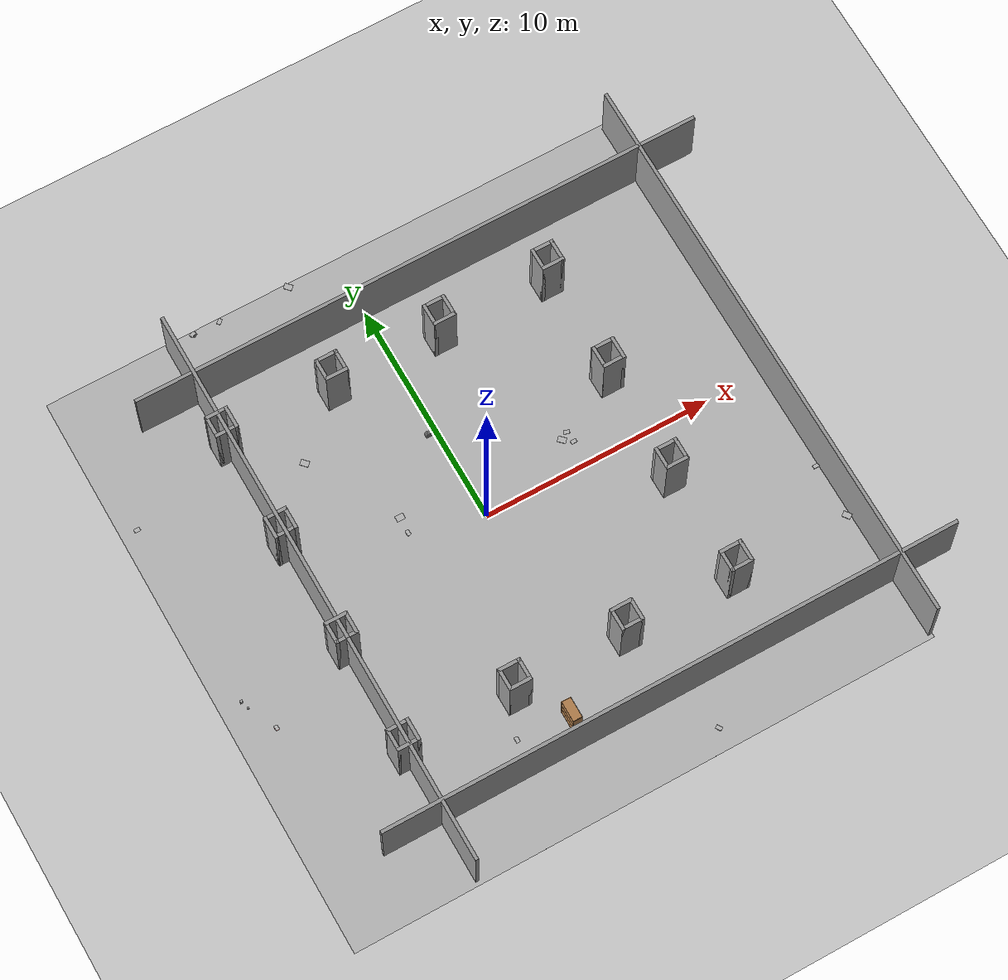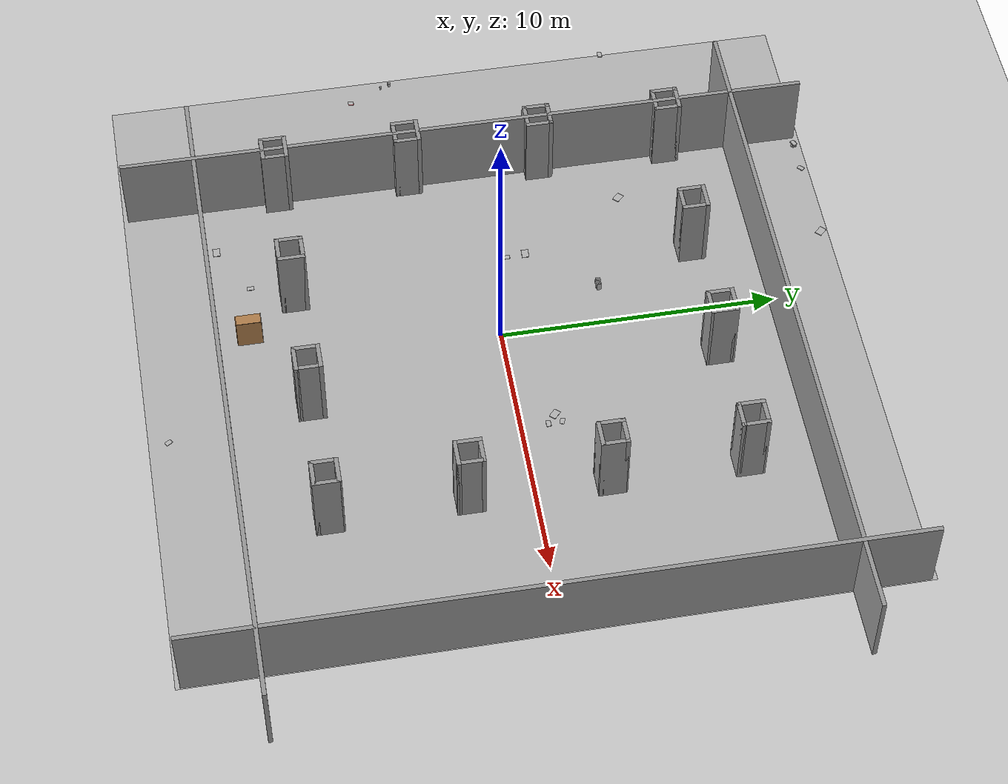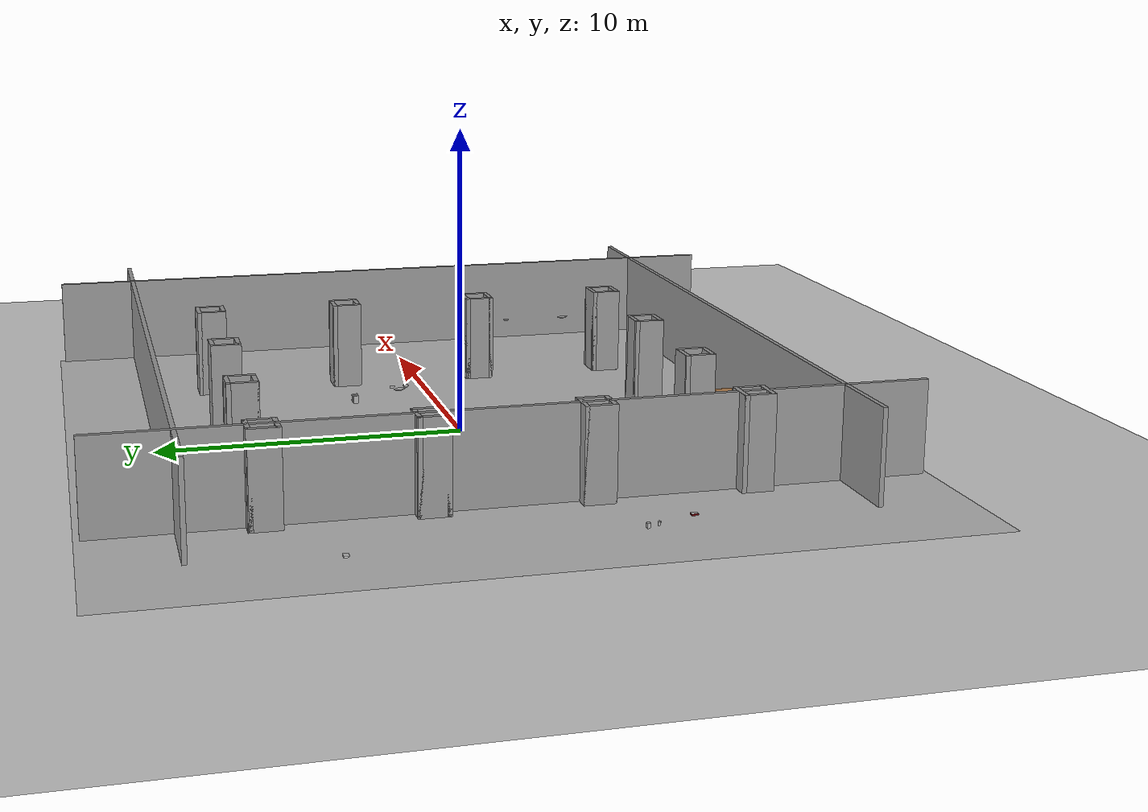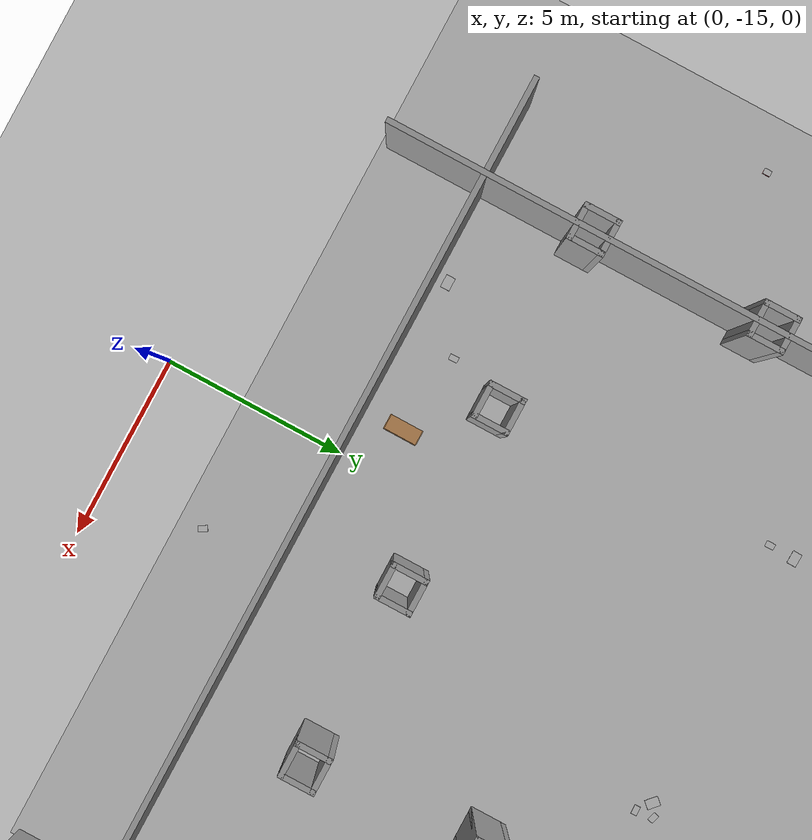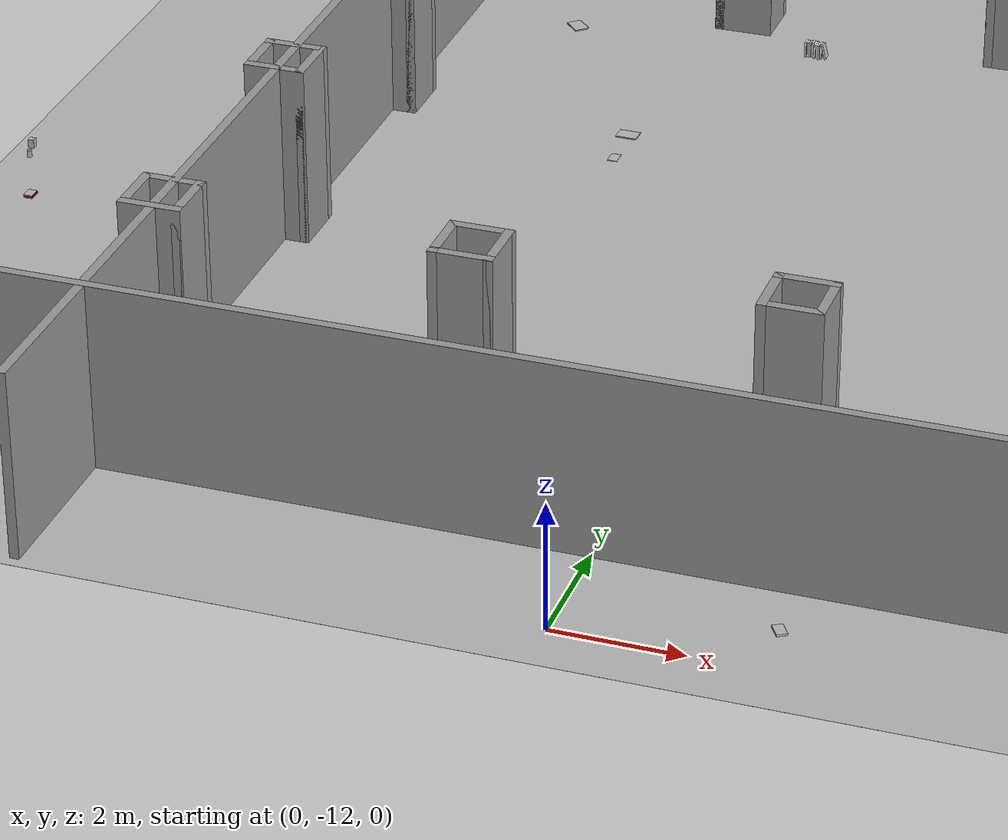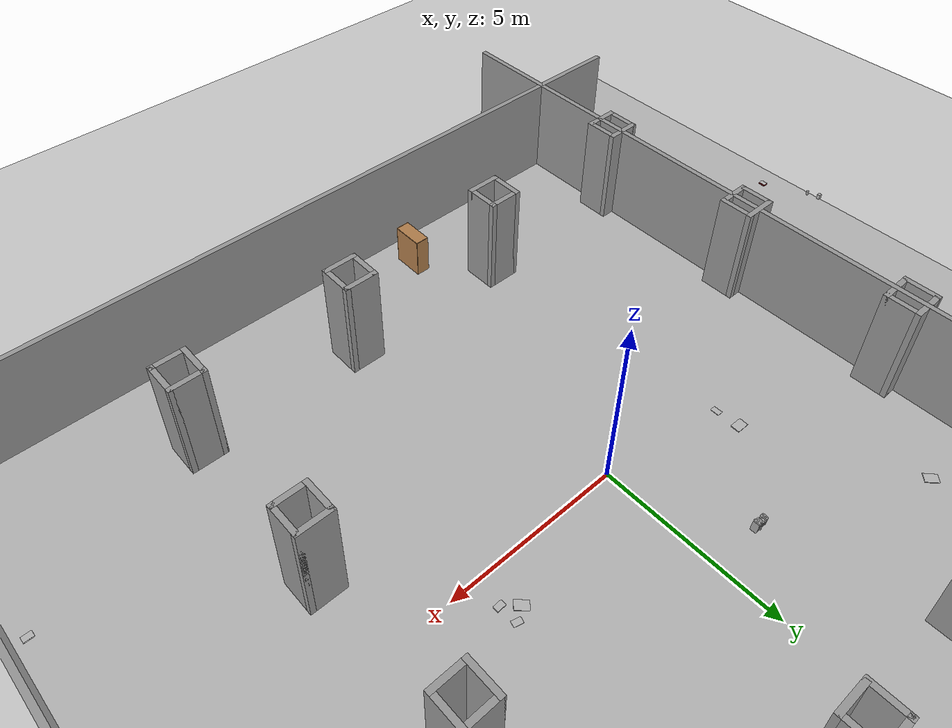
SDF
<sdf version="1.6">
 <world name="default">
  <scene><shadows>0</shadows><ambient>0.4 0.4 0.4 1</ambient><background>0 0 0 1</background></scene>
  <light name="sun" type="directional">
   <cast_shadows>0</cast_shadows>
   <pose>0 0 5 0 -0 0</pose>
   <diffuse>0.8 0.8 0.8 1</diffuse>
   <specular>0.1 0.1 0.1 1</specular>
   <attenuation>
    <range>1000</range>
    <constant>0.9</constant>
    <linear>0.01</linear>
    <quadratic>0.001</quadratic>
   </attenuation>
   <direction>-0.5 0.5 -1</direction>
  </light>
  <physics name="default_physics" default="0" type="ode">
   <max_step_size>0.001</max_step_size>
   <real_time_factor>1</real_time_factor>
   <real_time_update_rate>1000</real_time_update_rate>
  </physics>
  <scene><ambient>0.4 0.4 0.4 1</ambient><background>0.7 0.7 0.7 1</background><shadows>1</shadows></scene>
  <spherical_coordinates>
   <surface_model>EARTH_WGS84</surface_model>
   <latitude_deg>0</latitude_deg>
   <longitude_deg>0</longitude_deg>
   <elevation>0</elevation>
   <heading_deg>0</heading_deg>
  </spherical_coordinates>
  <model name="ground_plane">
   <static>1</static>
   <link name="link">
    <collision name="collision">
     <geometry><plane><normal>0 0 1</normal><size>100 100</size></plane></geometry>
     <surface><friction><ode><mu>1</mu><mu2>1</mu2></ode></friction></surface>
    </collision>
    <visual name="visual">
     <cast_shadows>0</cast_shadows>
     <geometry><plane><normal>0 0 1</normal><size>100 100</size></plane></geometry>
     <material>
      <script><uri>file://media/materials/scripts/gazebo.material</uri><name>Gazebo/Grey</name></script>
     </material>
    </visual>
    <velocity_decay><linear>0</linear><angular>0</angular></velocity_decay>
   </link>
  </model>
  <gravity>0 0 -9.8</gravity>
  <magnetic_field>6e-06 2.3e-05 -4.2e-05</magnetic_field>
  <atmosphere type="adiabatic"/>
  <model name="bookshelf">
   <static>1</static>
   <link name="link">
    <inertial><mass>1</mass></inertial>
    <collision name="back">
     <pose>0 0.005 0.6 0 -0 0</pose>
     <geometry><box><size>0.9 0.01 1.2</size></box></geometry>
    </collision>
    <visual name="visual1">
     <pose>0 0.005 0.6 0 -0 0</pose>
     <geometry><box><size>0.9 0.01 1.2</size></box></geometry>
     <material>
      <script><uri>file://media/materials/scripts/gazebo.material</uri><name>Gazebo/Wood</name></script>
     </material>
    </visual>
    <collision name="left_side">
     <pose>0.45 -0.195 0.6 0 -0 0</pose>
     <geometry><box><size>0.02 0.4 1.2</size></box></geometry>
    </collision>
    <visual name="visual2">
     <pose>0.45 -0.195 0.6 0 -0 0</pose>
     <geometry><box><size>0.02 0.4 1.2</size></box></geometry>
     <material>
      <script><uri>file://media/materials/scripts/gazebo.material</uri><name>Gazebo/Wood</name></script>
     </material>
    </visual>
    <collision name="right_side">
     <pose>-0.45 -0.195 0.6 0 -0 0</pose>
     <geometry><box><size>0.02 0.4 1.2</size></box></geometry>
    </collision>
    <visual name="visual3">
     <pose>-0.45 -0.195 0.6 0 -0 0</pose>
     <geometry><box><size>0.02 0.4 1.2</size></box></geometry>
     <material>
      <script><uri>file://media/materials/scripts/gazebo.material</uri><name>Gazebo/Wood</name></script>
     </material>
    </visual>
    <collision name="bottom">
     <pose>0 -0.195 0.03 0 -0 0</pose>
     <geometry><box><size>0.88 0.4 0.06</size></box></geometry>
    </collision>
    <visual name="visual4">
     <pose>0 -0.195 0.03 0 -0 0</pose>
     <geometry><box><size>0.88 0.4 0.06</size></box></geometry>
     <material>
      <script><uri>file://media/materials/scripts/gazebo.material</uri><name>Gazebo/Wood</name></script>
     </material>
    </visual>
    <collision name="top">
     <pose>0 -0.195 1.19 0 -0 0</pose>
     <geometry><box><size>0.88 0.4 0.02</size></box></geometry>
    </collision>
    <visual name="visual5">
     <pose>0 -0.195 1.19 0 -0 0</pose>
     <geometry><box><size>0.88 0.4 0.02</size></box></geometry>
     <material>
      <script><uri>file://media/materials/scripts/gazebo.material</uri><name>Gazebo/Wood</name></script>
     </material>
    </visual>
    <collision name="low_shelf">
     <pose>0 -0.195 0.43 0 -0 0</pose>
     <geometry><box><size>0.88 0.4 0.02</size></box></geometry>
    </collision>
    <visual name="visual6">
     <pose>0 -0.195 0.43 0 -0 0</pose>
     <geometry><box><size>0.88 0.4 0.02</size></box></geometry>
     <material>
      <script><uri>file://media/materials/scripts/gazebo.material</uri><name>Gazebo/Wood</name></script>
     </material>
    </visual>
    <collision name="high_shelf">
     <pose>0 -0.195 0.8 0 -0 0</pose>
     <geometry><box><size>0.88 0.4 0.02</size></box></geometry>
    </collision>
    <visual name="visual7">
     <pose>0 -0.195 0.8 0 -0 0</pose>
     <geometry><box><size>0.88 0.4 0.02</size></box></geometry>
     <material>
      <script><uri>file://media/materials/scripts/gazebo.material</uri><name>Gazebo/Wood</name></script>
     </material>
    </visual>
   </link>
   <pose>-1.09334 -8.8632 -0.00077 0 0 -1.57549</pose>
  </model>
  <model name="book_10">
   <link name="cover">
    <pose>0 -0.000108 0.015405 0 -0 0</pose>
    <visual name="visual">
     <geometry><box><size>0.245 0.16 0.03</size></box></geometry>
     <material>
      <script>
       <uri>model://book_10/materials/scripts</uri>
       <uri>model://book_10/materials/textures</uri>
       <name>book_10</name>
      </script>
     </material>
    </visual>
    <collision name="collision"><geometry><box><size>0.245 0.16 0.03</size></box></geometry></collision>
   </link>
   <link name="page">
    <pose>0 0.000608 0.015405 0 -0 0</pose>
    <visual name="visual">
     <geometry><box><size>0.24502 0.15862 0.028</size></box></geometry>
     <material>
      <lighting>1</lighting>
      <ambient>1 1 1 1</ambient>
      <diffuse>1 1 1 1</diffuse>
      <specular>0.01 0.01 0.01 1</specular>
      <emissive>0 0 0 1</emissive>
      <shader type="vertex"><normal_map>__default__</normal_map></shader>
     </material>
    </visual>
    <collision name="collision"><geometry><box><size>0.245 0.16 0.03</size></box></geometry></collision>
   </link>
   <static>1</static>
   <pose>-0.704711 3.6032 1.53413 2.29078 1.52264 -0.882053</pose>
  </model>
  <model name="book_1">
   <link name="cover">
    <pose>0 -0.000108 0.015405 0 -0 0</pose>
    <visual name="visual">
     <geometry><box><size>0.245 0.16 0.03</size></box></geometry>
     <material>
      <script>
       <uri>model://book_1/materials/scripts</uri>
       <uri>model://book_1/materials/textures</uri>
       <name>book_1</name>
      </script>
     </material>
    </visual>
    <collision name="collision"><geometry><box><size>0.245 0.16 0.03</size></box></geometry></collision>
   </link>
   <link name="page">
    <pose>0 0.000608 0.015405 0 -0 0</pose>
    <visual name="visual">
     <geometry><box><size>0.24502 0.15862 0.028</size></box></geometry>
     <material>
      <lighting>1</lighting>
      <ambient>1 1 1 1</ambient>
      <diffuse>1 1 1 1</diffuse>
      <specular>0.01 0.01 0.01 1</specular>
      <emissive>0 0 0 1</emissive>
      <shader type="vertex"><normal_map>__default__</normal_map></shader>
     </material>
    </visual>
    <collision name="collision"><geometry><box><size>0.245 0.16 0.03</size></box></geometry></collision>
   </link>
   <static>1</static>
   <pose>-0.631207 3.60794 1.53446 1.82543 1.45034 -1.33497</pose>
  </model>
  <model name="book_11">
   <link name="cover">
    <pose>0 -0.000108 0.015405 0 -0 0</pose>
    <visual name="visual">
     <geometry><box><size>0.245 0.16 0.03</size></box></geometry>
     <material>
      <script>
       <uri>model://book_11/materials/scripts</uri>
       <uri>model://book_11/materials/textures</uri>
       <name>book_11</name>
      </script>
     </material>
    </visual>
    <collision name="collision"><geometry><box><size>0.245 0.16 0.03</size></box></geometry></collision>
   </link>
   <link name="page">
    <pose>0 0.000608 0.015405 0 -0 0</pose>
    <visual name="visual">
     <geometry><box><size>0.24502 0.15862 0.028</size></box></geometry>
     <material>
      <lighting>1</lighting>
      <ambient>1 1 1 1</ambient>
      <diffuse>1 1 1 1</diffuse>
      <specular>0.01 0.01 0.01 1</specular>
      <emissive>0 0 0 1</emissive>
      <shader type="vertex"><normal_map>__default__</normal_map></shader>
     </material>
    </visual>
    <collision name="collision"><geometry><box><size>0.245 0.16 0.03</size></box></geometry></collision>
   </link>
   <static>1</static>
   <pose>-0.518519 3.60919 1.52712 -1.58338 1.55387 1.5988</pose>
  </model>
  <model name="book_12">
   <link name="cover">
    <pose>0 -0.000108 0.015405 0 -0 0</pose>
    <visual name="visual">
     <geometry><box><size>0.245 0.16 0.03</size></box></geometry>
     <material>
      <script>
       <uri>model://book_12/materials/scripts</uri>
       <uri>model://book_12/materials/textures</uri>
       <name>book_12</name>
      </script>
     </material>
    </visual>
    <collision name="collision"><geometry><box><size>0.245 0.16 0.03</size></box></geometry></collision>
   </link>
   <link name="page">
    <pose>0 0.000608 0.015405 0 -0 0</pose>
    <visual name="visual">
     <geometry><box><size>0.24502 0.15862 0.028</size></box></geometry>
     <material>
      <lighting>1</lighting>
      <ambient>1 1 1 1</ambient>
      <diffuse>1 1 1 1</diffuse>
      <specular>0.01 0.01 0.01 1</specular>
      <emissive>0 0 0 1</emissive>
      <shader type="vertex"><normal_map>__default__</normal_map></shader>
     </material>
    </visual>
    <collision name="collision"><geometry><box><size>0.245 0.16 0.03</size></box></geometry></collision>
   </link>
   <static>1</static>
   <pose>-0.483517 3.58624 1.52353 -2.04149 1.53654 1.10687</pose>
  </model>
  <model name="book_14">
   <link name="cover">
    <pose>0 -0.000108 0.015405 0 -0 0</pose>
    <visual name="visual">
     <geometry><box><size>0.245 0.16 0.03</size></box></geometry>
     <material>
      <script>
       <uri>model://book_14/materials/scripts</uri>
       <uri>model://book_14/materials/textures</uri>
       <name>book_14</name>
      </script>
     </material>
    </visual>
    <collision name="collision"><geometry><box><size>0.245 0.16 0.03</size></box></geometry></collision>
   </link>
   <link name="page">
    <pose>0 0.000608 0.015405 0 -0 0</pose>
    <visual name="visual">
     <geometry><box><size>0.24502 0.15862 0.028</size></box></geometry>
     <material>
      <lighting>1</lighting>
      <ambient>1 1 1 1</ambient>
      <diffuse>1 1 1 1</diffuse>
      <specular>0.01 0.01 0.01 1</specular>
      <emissive>0 0 0 1</emissive>
      <shader type="vertex"><normal_map>__default__</normal_map></shader>
     </material>
    </visual>
    <collision name="collision"><geometry><box><size>0.245 0.16 0.03</size></box></geometry></collision>
   </link>
   <static>1</static>
   <pose>-0.397337 3.60071 1.53368 -3.08906 1.34097 0.077504</pose>
  </model>
  <model name="book_15">
   <link name="cover">
    <pose>0 -0.000108 0.015405 0 -0 0</pose>
    <visual name="visual">
     <geometry><box><size>0.245 0.16 0.03</size></box></geometry>
     <material>
      <script>
       <uri>model://book_15/materials/scripts</uri>
       <uri>model://book_15/materials/textures</uri>
       <name>book_15</name>
      </script>
     </material>
    </visual>
    <collision name="collision"><geometry><box><size>0.245 0.16 0.03</size></box></geometry></collision>
   </link>
   <link name="page">
    <pose>0 0.000608 0.015405 0 -0 0</pose>
    <visual name="visual">
     <geometry><box><size>0.24502 0.15862 0.028</size></box></geometry>
     <material>
      <lighting>1</lighting>
      <ambient>1 1 1 1</ambient>
      <diffuse>1 1 1 1</diffuse>
      <specular>0.01 0.01 0.01 1</specular>
      <emissive>0 0 0 1</emissive>
      <shader type="vertex"><normal_map>__default__</normal_map></shader>
     </material>
    </visual>
    <collision name="collision"><geometry><box><size>0.245 0.16 0.03</size></box></geometry></collision>
   </link>
   <static>1</static>
   <pose>-0.668325 3.60522 1.53259 2.04938 1.50294 -1.04077</pose>
  </model>
  <model name="book_16">
   <link name="cover">
    <pose>0 -0.000108 0.015405 0 -0 0</pose>
    <visual name="visual">
     <geometry><box><size>0.245 0.16 0.03</size></box></geometry>
     <material>
      <script>
       <uri>model://book_16/materials/scripts</uri>
       <uri>model://book_16/materials/textures</uri>
       <name>book_16</name>
      </script>
     </material>
    </visual>
    <collision name="collision"><geometry><box><size>0.245 0.16 0.03</size></box></geometry></collision>
   </link>
   <link name="page">
    <pose>0 0.000608 0.015405 0 -0 0</pose>
    <visual name="visual">
     <geometry><box><size>0.24502 0.15862 0.028</size></box></geometry>
     <material>
      <lighting>1</lighting>
      <ambient>1 1 1 1</ambient>
      <diffuse>1 1 1 1</diffuse>
      <specular>0.01 0.01 0.01 1</specular>
      <emissive>0 0 0 1</emissive>
      <shader type="vertex"><normal_map>__default__</normal_map></shader>
     </material>
    </visual>
    <collision name="collision"><geometry><box><size>0.245 0.16 0.03</size></box></geometry></collision>
   </link>
   <static>1</static>
   <pose>4.42601 0.923836 0.431684 0 0 -3.11812</pose>
  </model>
  <model name="book_17">
   <link name="cover">
    <pose>0 -0.000108 0.015405 0 -0 0</pose>
    <visual name="visual">
     <geometry><box><size>0.245 0.16 0.03</size></box></geometry>
     <material>
      <script>
       <uri>model://book_17/materials/scripts</uri>
       <uri>model://book_17/materials/textures</uri>
       <name>book_17</name>
      </script>
     </material>
    </visual>
    <collision name="collision"><geometry><box><size>0.245 0.16 0.03</size></box></geometry></collision>
   </link>
   <link name="page">
    <pose>0 0.000608 0.015405 0 -0 0</pose>
    <visual name="visual">
     <geometry><box><size>0.24502 0.15862 0.028</size></box></geometry>
     <material>
      <lighting>1</lighting>
      <ambient>1 1 1 1</ambient>
      <diffuse>1 1 1 1</diffuse>
      <specular>0.01 0.01 0.01 1</specular>
      <emissive>0 0 0 1</emissive>
      <shader type="vertex"><normal_map>__default__</normal_map></shader>
     </material>
    </visual>
    <collision name="collision"><geometry><box><size>0.245 0.16 0.03</size></box></geometry></collision>
   </link>
   <static>1</static>
   <pose>-0.556135 3.60459 1.5276 0.63624 1.49937 -2.46109</pose>
  </model>
  <model name="book_18">
   <link name="cover">
    <pose>0 -0.000108 0.015405 0 -0 0</pose>
    <visual name="visual">
     <geometry><box><size>0.245 0.16 0.03</size></box></geometry>
     <material>
      <script>
       <uri>model://book_18/materials/scripts</uri>
       <uri>model://book_18/materials/textures</uri>
       <name>book_18</name>
      </script>
     </material>
    </visual>
    <collision name="collision"><geometry><box><size>0.245 0.16 0.03</size></box></geometry></collision>
   </link>
   <link name="page">
    <pose>0 0.000608 0.015405 0 -0 0</pose>
    <visual name="visual">
     <geometry><box><size>0.24502 0.15862 0.028</size></box></geometry>
     <material>
      <lighting>1</lighting>
      <ambient>1 1 1 1</ambient>
      <diffuse>1 1 1 1</diffuse>
      <specular>0.01 0.01 0.01 1</specular>
      <emissive>0 0 0 1</emissive>
      <shader type="vertex"><normal_map>__default__</normal_map></shader>
     </material>
    </visual>
    <collision name="collision"><geometry><box><size>0.245 0.16 0.03</size></box></geometry></collision>
   </link>
   <static>1</static>
   <pose>-0.450242 3.60603 1.53141 1.91107 1.46152 -1.1576</pose>
  </model>
  <model name="book_2">
   <link name="cover">
    <pose>0 -0.000108 0.015405 0 -0 0</pose>
    <visual name="visual">
     <geometry><box><size>0.245 0.16 0.03</size></box></geometry>
     <material>
      <script>
       <uri>model://book_2/materials/scripts</uri>
       <uri>model://book_2/materials/textures</uri>
       <name>book_2</name>
      </script>
     </material>
    </visual>
    <collision name="collision"><geometry><box><size>0.245 0.16 0.03</size></box></geometry></collision>
   </link>
   <link name="page">
    <pose>0 0.000608 0.015405 0 -0 0</pose>
    <visual name="visual">
     <geometry><box><size>0.24502 0.15862 0.028</size></box></geometry>
     <material>
      <lighting>1</lighting>
      <ambient>1 1 1 1</ambient>
      <diffuse>1 1 1 1</diffuse>
      <specular>0.01 0.01 0.01 1</specular>
      <emissive>0 0 0 1</emissive>
      <shader type="vertex"><normal_map>__default__</normal_map></shader>
     </material>
    </visual>
    <collision name="collision"><geometry><box><size>0.245 0.16 0.03</size></box></geometry></collision>
   </link>
   <static>1</static>
   <pose>-0.5901 3.60851 1.53925 1.41428 1.38931 -1.69021</pose>
  </model>
  <model name="book_20">
   <link name="cover">
    <pose>0 -0.000108 0.015405 0 -0 0</pose>
    <visual name="visual">
     <geometry><box><size>0.245 0.16 0.03</size></box></geometry>
     <material>
      <script>
       <uri>model://book_20/materials/scripts</uri>
       <uri>model://book_20/materials/textures</uri>
       <name>book_20</name>
      </script>
     </material>
    </visual>
    <collision name="collision"><geometry><box><size>0.245 0.16 0.03</size></box></geometry></collision>
   </link>
   <link name="page">
    <pose>0 0.000608 0.015405 0 -0 0</pose>
    <visual name="visual">
     <geometry><box><size>0.24502 0.15862 0.028</size></box></geometry>
     <material>
      <lighting>1</lighting>
      <ambient>1 1 1 1</ambient>
      <diffuse>1 1 1 1</diffuse>
      <specular>0.01 0.01 0.01 1</specular>
      <emissive>0 0 0 1</emissive>
      <shader type="vertex"><normal_map>__default__</normal_map></shader>
     </material>
    </visual>
    <collision name="collision"><geometry><box><size>0.245 0.16 0.03</size></box></geometry></collision>
   </link>
   <static>1</static>
   <pose>-1.33514 -8.47354 0.933303 -3.1415 -1.50452 1.64295</pose>
  </model>
  <model name="book_21">
   <link name="cover">
    <pose>0 -0.000108 0.005 0 -0 0</pose>
    <visual name="visual">
     <geometry><box><size>0.245 0.16 0.01</size></box></geometry>
     <material>
      <script>
       <uri>model://book_21/materials/scripts</uri>
       <uri>model://book_21/materials/textures</uri>
       <name>book_21</name>
      </script>
     </material>
    </visual>
    <collision name="collision"><geometry><box><size>0.245 0.16 0.01</size></box></geometry></collision>
   </link>
   <link name="page">
    <pose>0 0.000608 0.005 0 -0 0</pose>
    <visual name="visual">
     <geometry><box><size>0.24502 0.15862 0.008</size></box></geometry>
     <material>
      <lighting>1</lighting>
      <ambient>1 1 1 1</ambient>
      <diffuse>1 1 1 1</diffuse>
      <specular>0.01 0.01 0.01 1</specular>
      <emissive>0 0 0 1</emissive>
      <shader type="vertex"><normal_map>__default__</normal_map></shader>
     </material>
    </visual>
    <collision name="collision"><geometry><box><size>0.245 0.16 0.008</size></box></geometry></collision>
   </link>
   <static>1</static>
   <pose>-1.32998 -8.52484 0.933 -3.13832 -1.32475 1.56842</pose>
  </model>
  <model name="book_3">
   <link name="cover">
    <pose>0 -0.000108 0.01 0 -0 0</pose>
    <visual name="visual">
     <geometry><box><size>0.245 0.16 0.02</size></box></geometry>
     <material>
      <script>
       <uri>model://book_3/materials/scripts</uri>
       <uri>model://book_3/materials/textures</uri>
       <name>book_3</name>
      </script>
     </material>
    </visual>
    <collision name="collision"><geometry><box><size>0.245 0.16 0.02</size></box></geometry></collision>
   </link>
   <link name="page">
    <pose>0 0.000608 0.01 0 -0 0</pose>
    <visual name="visual">
     <geometry><box><size>0.24502 0.15862 0.018</size></box></geometry>
     <material>
      <lighting>1</lighting>
      <ambient>1 1 1 1</ambient>
      <diffuse>1 1 1 1</diffuse>
      <specular>0.01 0.01 0.01 1</specular>
      <emissive>0 0 0 1</emissive>
      <shader type="vertex"><normal_map>__default__</normal_map></shader>
     </material>
    </visual>
    <collision name="collision"><geometry><box><size>0.245 0.16 0.018</size></box></geometry></collision>
   </link>
   <static>1</static>
   <pose>-1.34027 -8.59409 0.94392 -3.1394 -1.1994 1.56955</pose>
  </model>
  <model name="book_4">
   <link name="cover">
    <pose>0 -0.000108 0.01 0 -0 0</pose>
    <visual name="visual">
     <geometry><box><size>0.245 0.16 0.02</size></box></geometry>
     <material>
      <script>
       <uri>model://book_4/materials/scripts</uri>
       <uri>model://book_4/materials/textures</uri>
       <name>book_4</name>
      </script>
     </material>
     <cast_shadows>0</cast_shadows>
    </visual>
    <collision name="collision"><geometry><box><size>0.245 0.16 0.02</size></box></geometry></collision>
   </link>
   <link name="page">
    <pose>0 0.000608 0.01 0 -0 0</pose>
    <visual name="visual">
     <geometry><box><size>0.24502 0.15862 0.018</size></box></geometry>
     <material>
      <lighting>1</lighting>
      <ambient>1 1 1 1</ambient>
      <diffuse>1 1 1 1</diffuse>
      <specular>0.01 0.01 0.01 1</specular>
      <emissive>0 0 0 1</emissive>
      <shader type="vertex"><normal_map>__default__</normal_map></shader>
     </material>
     <cast_shadows>0</cast_shadows>
    </visual>
    <collision name="collision"><geometry><box><size>0.245 0.16 0.018</size></box></geometry></collision>
   </link>
   <static>1</static>
   <pose>-1.33002 -8.62073 0.934243 -3.13946 -1.18764 1.56962</pose>
  </model>
  <model name="book_9">
   <link name="cover">
    <pose>0 -0.000108 0.005 0 -0 0</pose>
    <visual name="visual">
     <geometry><box><size>0.245 0.16 0.01</size></box></geometry>
     <material>
      <script>
       <uri>model://book_9/materials/scripts</uri>
       <uri>model://book_9/materials/textures</uri>
       <name>book_9</name>
      </script>
     </material>
    </visual>
    <collision name="collision"><geometry><box><size>0.245 0.16 0.01</size></box></geometry></collision>
   </link>
   <link name="page">
    <pose>0 0.000608 0.005 0 -0 0</pose>
    <visual name="visual">
     <geometry><box><size>0.24502 0.15862 0.008</size></box></geometry>
     <material>
      <lighting>1</lighting>
      <ambient>1 1 1 1</ambient>
      <diffuse>1 1 1 1</diffuse>
      <specular>0.01 0.01 0.01 1</specular>
      <emissive>0 0 0 1</emissive>
      <shader type="vertex"><normal_map>__default__</normal_map></shader>
     </material>
    </visual>
    <collision name="collision"><geometry><box><size>0.245 0.16 0.008</size></box></geometry></collision>
   </link>
   <static>1</static>
   <pose>-1.32998 -8.49338 0.933 -3.13349 -1.47234 1.57155</pose>
  </model>
  <model name="book_16_0">
   <link name="cover">
    <pose>0 -0.000108 0.015405 0 -0 0</pose>
    <visual name="visual">
     <geometry><box><size>0.245 0.16 0.03</size></box></geometry>
     <material>
      <script>
       <uri>model://book_16/materials/scripts</uri>
       <uri>model://book_16/materials/textures</uri>
       <name>book_16</name>
      </script>
     </material>
    </visual>
    <collision name="collision"><geometry><box><size>0.245 0.16 0.03</size></box></geometry></collision>
   </link>
   <link name="page">
    <pose>0 0.000608 0.015405 0 -0 0</pose>
    <visual name="visual">
     <geometry><box><size>0.24502 0.15862 0.028</size></box></geometry>
     <material>
      <lighting>1</lighting>
      <ambient>1 1 1 1</ambient>
      <diffuse>1 1 1 1</diffuse>
      <specular>0.01 0.01 0.01 1</specular>
      <emissive>0 0 0 1</emissive>
      <shader type="vertex"><normal_map>__default__</normal_map></shader>
     </material>
    </visual>
    <collision name="collision"><geometry><box><size>0.245 0.16 0.03</size></box></geometry></collision>
   </link>
   <static>1</static>
   <pose>-1.32786 -8.56422 0.936359 -3.13881 -1.28012 1.56893</pose>
  </model>
  <model name="book_13">
   <link name="cover">
    <pose>0 -0.000108 0.015405 0 -0 0</pose>
    <visual name="visual">
     <geometry><box><size>0.245 0.16 0.03</size></box></geometry>
     <material>
      <script>
       <uri>model://book_13/materials/scripts</uri>
       <uri>model://book_13/materials/textures</uri>
       <name>book_13</name>
      </script>
     </material>
    </visual>
    <collision name="collision"><geometry><box><size>0.245 0.16 0.03</size></box></geometry></collision>
   </link>
   <link name="page">
    <pose>0 0.000608 0.015405 0 -0 0</pose>
    <visual name="visual">
     <geometry><box><size>0.24502 0.15862 0.028</size></box></geometry>
     <material>
      <lighting>1</lighting>
      <ambient>1 1 1 1</ambient>
      <diffuse>1 1 1 1</diffuse>
      <specular>0.01 0.01 0.01 1</specular>
      <emissive>0 0 0 1</emissive>
      <shader type="vertex"><normal_map>__default__</normal_map></shader>
     </material>
    </visual>
    <collision name="collision"><geometry><box><size>0.245 0.16 0.03</size></box></geometry></collision>
   </link>
   <static>1</static>
   <pose>-1.33006 -8.72144 0.935666 -3.13982 -1.10393 1.57001</pose>
  </model>
  <model name="book_12_0">
   <link name="cover">
    <pose>0 -0.000108 0.015405 0 -0 0</pose>
    <visual name="visual">
     <geometry><box><size>0.245 0.16 0.03</size></box></geometry>
     <material>
      <script>
       <uri>model://book_12/materials/scripts</uri>
       <uri>model://book_12/materials/textures</uri>
       <name>book_12</name>
      </script>
     </material>
    </visual>
    <collision name="collision"><geometry><box><size>0.245 0.16 0.03</size></box></geometry></collision>
   </link>
   <link name="page">
    <pose>0 0.000608 0.015405 0 -0 0</pose>
    <visual name="visual">
     <geometry><box><size>0.24502 0.15862 0.028</size></box></geometry>
     <material>
      <lighting>1</lighting>
      <ambient>1 1 1 1</ambient>
      <diffuse>1 1 1 1</diffuse>
      <specular>0.01 0.01 0.01 1</specular>
      <emissive>0 0 0 1</emissive>
      <shader type="vertex"><normal_map>__default__</normal_map></shader>
     </material>
    </visual>
    <collision name="collision"><geometry><box><size>0.245 0.16 0.03</size></box></geometry></collision>
   </link>
   <static>1</static>
   <pose>-1.33007 -8.75802 0.937574 -3.13986 -1.0924 1.57006</pose>
  </model>
  <model name="book_6">
   <link name="cover">
    <pose>0 -0.000108 0.01 0 -0 0</pose>
    <visual name="visual">
     <geometry><box><size>0.245 0.16 0.02</size></box></geometry>
     <material>
      <script>
       <uri>model://book_6/materials/scripts</uri>
       <uri>model://book_6/materials/textures</uri>
       <name>book_6</name>
      </script>
     </material>
    </visual>
    <collision name="collision"><geometry><box><size>0.245 0.16 0.02</size></box></geometry></collision>
   </link>
   <link name="page">
    <pose>0 0.000608 0.01 0 -0 0</pose>
    <visual name="visual">
     <geometry><box><size>0.24502 0.15862 0.018</size></box></geometry>
     <material>
      <lighting>1</lighting>
      <ambient>1 1 1 1</ambient>
      <diffuse>1 1 1 1</diffuse>
      <specular>0.01 0.01 0.01 1</specular>
      <emissive>0 0 0 1</emissive>
      <shader type="vertex"><normal_map>__default__</normal_map></shader>
     </material>
    </visual>
    <collision name="collision"><geometry><box><size>0.245 0.16 0.018</size></box></geometry></collision>
   </link>
   <static>1</static>
   <pose>-1.33004 -8.64658 0.937038 -3.13966 -1.14492 1.56984</pose>
  </model>
  <model name="book_8">
   <link name="cover">
    <pose>0 -0.000108 0.005 0 -0 0</pose>
    <visual name="visual">
     <geometry><box><size>0.245 0.16 0.01</size></box></geometry>
     <material>
      <script>
       <uri>model://book_8/materials/scripts</uri>
       <uri>model://book_8/materials/textures</uri>
       <name>book_8</name>
      </script>
     </material>
    </visual>
    <collision name="collision"><geometry><box><size>0.245 0.16 0.01</size></box></geometry></collision>
   </link>
   <link name="page">
    <pose>0 0.000608 0.005 0 -0 0</pose>
    <visual name="visual">
     <geometry><box><size>0.24502 0.15862 0.008</size></box></geometry>
     <material>
      <lighting>1</lighting>
      <ambient>1 1 1 1</ambient>
      <diffuse>1 1 1 1</diffuse>
      <specular>0.01 0.01 0.01 1</specular>
      <emissive>0 0 0 1</emissive>
      <shader type="vertex"><normal_map>__default__</normal_map></shader>
     </material>
    </visual>
    <collision name="collision"><geometry><box><size>0.245 0.16 0.008</size></box></geometry></collision>
   </link>
   <static>1</static>
   <pose>4.38842 1.42121 0.431029 0 -0 2.87142</pose>
  </model>
  <model name="book_19">
   <link name="cover">
    <pose>0 -0.000108 0.015405 0 -0 0</pose>
    <visual name="visual">
     <geometry><box><size>0.245 0.16 0.03</size></box></geometry>
     <material>
      <script>
       <uri>model://book_19/materials/scripts</uri>
       <uri>model://book_19/materials/textures</uri>
       <name>book_19</name>
      </script>
     </material>
    </visual>
    <collision name="collision"><geometry><box><size>0.245 0.16 0.03</size></box></geometry></collision>
   </link>
   <link name="page">
    <pose>0 0.000608 0.015405 0 -0 0</pose>
    <visual name="visual">
     <geometry><box><size>0.24502 0.15862 0.028</size></box></geometry>
     <material>
      <lighting>1</lighting>
      <ambient>1 1 1 1</ambient>
      <diffuse>1 1 1 1</diffuse>
      <specular>0.01 0.01 0.01 1</specular>
      <emissive>0 0 0 1</emissive>
      <shader type="vertex"><normal_map>__default__</normal_map></shader>
     </material>
    </visual>
    <collision name="collision"><geometry><box><size>0.245 0.16 0.03</size></box></geometry></collision>
   </link>
   <static>1</static>
   <pose>-1.32315 -8.68246 0.939077 -3.13968 -1.14225 1.56985</pose>
  </model>
  <model name="book_13_0">
   <link name="cover">
    <pose>0 -0.000108 0.015405 0 -0 0</pose>
    <visual name="visual">
     <geometry><box><size>0.245 0.16 0.03</size></box></geometry>
     <material>
      <script>
       <uri>model://book_13/materials/scripts</uri>
       <uri>model://book_13/materials/textures</uri>
       <name>book_13</name>
      </script>
     </material>
    </visual>
    <collision name="collision"><geometry><box><size>0.245 0.16 0.03</size></box></geometry></collision>
   </link>
   <link name="page">
    <pose>0 0.000608 0.015405 0 -0 0</pose>
    <visual name="visual">
     <geometry><box><size>0.24502 0.15862 0.028</size></box></geometry>
     <material>
      <lighting>1</lighting>
      <ambient>1 1 1 1</ambient>
      <diffuse>1 1 1 1</diffuse>
      <specular>0.01 0.01 0.01 1</specular>
      <emissive>0 0 0 1</emissive>
      <shader type="vertex"><normal_map>__default__</normal_map></shader>
     </material>
    </visual>
    <collision name="collision"><geometry><box><size>0.245 0.16 0.03</size></box></geometry></collision>
   </link>
   <static>1</static>
   <pose>-1.33008 -8.84522 0.930105 -3.14009 -1.01364 1.57031</pose>
  </model>
  <model name="book_14_0">
   <link name="cover">
    <pose>0 -0.000108 0.015405 0 -0 0</pose>
    <visual name="visual">
     <geometry><box><size>0.245 0.16 0.03</size></box></geometry>
     <material>
      <script>
       <uri>model://book_14/materials/scripts</uri>
       <uri>model://book_14/materials/textures</uri>
       <name>book_14</name>
      </script>
     </material>
    </visual>
    <collision name="collision"><geometry><box><size>0.245 0.16 0.03</size></box></geometry></collision>
   </link>
   <link name="page">
    <pose>0 0.000608 0.015405 0 -0 0</pose>
    <visual name="visual">
     <geometry><box><size>0.24502 0.15862 0.028</size></box></geometry>
     <material>
      <lighting>1</lighting>
      <ambient>1 1 1 1</ambient>
      <diffuse>1 1 1 1</diffuse>
      <specular>0.01 0.01 0.01 1</specular>
      <emissive>0 0 0 1</emissive>
      <shader type="vertex"><normal_map>__default__</normal_map></shader>
     </material>
    </visual>
    <collision name="collision"><geometry><box><size>0.245 0.16 0.03</size></box></geometry></collision>
   </link>
   <static>1</static>
   <pose>-1.33007 -8.8029 0.931916 -3.14002 -1.04019 1.57024</pose>
  </model>
  <model name="newspaper_1">
   <link name="link_0">
    <visual name="visual">
     <geometry><box><size>0.35 0.25 0.02</size></box></geometry>
     <material>
      <script>
       <uri>model://newspaper_1/materials/scripts</uri>
       <uri>model://newspaper_1/materials/textures</uri>
       <name>newspaper_1</name>
      </script>
     </material>
    </visual>
    <collision name="collision"><geometry><box><size>0.35 0.25 0.02</size></box></geometry></collision>
   </link>
   <static>1</static>
   <pose>-5.12924 -9.64405 0.455927 0 -0 0</pose>
  </model>
  <model name="book_6_0">
   <link name="cover">
    <pose>0 -0.000108 0.01 0 -0 0</pose>
    <visual name="visual">
     <geometry><box><size>0.245 0.16 0.02</size></box></geometry>
     <material>
      <script>
       <uri>model://book_6/materials/scripts</uri>
       <uri>model://book_6/materials/textures</uri>
       <name>book_6</name>
      </script>
     </material>
    </visual>
    <collision name="collision"><geometry><box><size>0.245 0.16 0.02</size></box></geometry></collision>
   </link>
   <link name="page">
    <pose>0 0.000608 0.01 0 -0 0</pose>
    <visual name="visual">
     <geometry><box><size>0.24502 0.15862 0.018</size></box></geometry>
     <material>
      <lighting>1</lighting>
      <ambient>1 1 1 1</ambient>
      <diffuse>1 1 1 1</diffuse>
      <specular>0.01 0.01 0.01 1</specular>
      <emissive>0 0 0 1</emissive>
      <shader type="vertex"><normal_map>__default__</normal_map></shader>
     </material>
    </visual>
    <collision name="collision"><geometry><box><size>0.245 0.16 0.018</size></box></geometry></collision>
   </link>
   <static>1</static>
   <pose>-3.52853 -8.59778 0.113948 0 -0 1.58993</pose>
  </model>
  <model name="coffee_box">
   <link name="link_0">
    <visual name="visual">
     <pose>0 0 0.06 0 -0 0</pose>
     <geometry><cylinder><radius>0.04</radius><length>0.12</length></cylinder></geometry>
     <material>
      <script>
       <uri>model://coffee_box/materials/scripts</uri>
       <uri>model://coffee_box/materials/textures</uri>
       <name>coffee_pat</name>
      </script>
     </material>
    </visual>
    <collision name="collision">
     <geometry><cylinder><radius>0.04</radius><length>0.12</length></cylinder></geometry>
    </collision>
   </link>
   <static>1</static>
   <pose>-11.9532 -2.63307 0.707355 0 -0 2.27574</pose>
  </model>
  <model name="tea_box">
   <link name="link">
    <pose>0 0 0.075 0 -0 0</pose>
    <visual name="visual">
     <geometry><box><size>0.1 0.1 0.15</size></box></geometry>
     <material>
      <script>
       <uri>model://tea_box/materials/scripts</uri>
       <uri>model://tea_box/materials/textures</uri>
       <name>tea_pat</name>
      </script>
     </material>
    </visual>
    <collision name="collision"><geometry><box><size>0.1 0.1 0.15</size></box></geometry></collision>
   </link>
   <static>1</static>
   <pose>-12.0637 -2.29001 0.698258 0 -0 0</pose>
  </model>
  <model name="book_9_0">
   <link name="cover">
    <pose>0 -0.000108 0.005 0 -0 0</pose>
    <visual name="visual">
     <geometry><box><size>0.245 0.16 0.01</size></box></geometry>
     <material>
      <script>
       <uri>model://book_9/materials/scripts</uri>
       <uri>model://book_9/materials/textures</uri>
       <name>book_9</name>
      </script>
     </material>
    </visual>
    <collision name="collision"><geometry><box><size>0.245 0.16 0.01</size></box></geometry></collision>
   </link>
   <link name="page">
    <pose>0 0.000608 0.005 0 -0 0</pose>
    <visual name="visual">
     <geometry><box><size>0.24502 0.15862 0.008</size></box></geometry>
     <material>
      <lighting>1</lighting>
      <ambient>1 1 1 1</ambient>
      <diffuse>1 1 1 1</diffuse>
      <specular>0.01 0.01 0.01 1</specular>
      <emissive>0 0 0 1</emissive>
      <shader type="vertex"><normal_map>__default__</normal_map></shader>
     </material>
    </visual>
    <collision name="collision"><geometry><box><size>0.245 0.16 0.008</size></box></geometry></collision>
   </link>
   <static>1</static>
   <pose>-3.1266 0.731411 0.499788 0 -0 1.5743</pose>
  </model>
  <model name="newspaper_2">
   <link name="link_0">
    <visual name="visual">
     <geometry><box><size>0.35 0.25 0.02</size></box></geometry>
     <material>
      <script>
       <uri>model://newspaper_2/materials/scripts</uri>
       <uri>model://newspaper_2/materials/textures</uri>
       <name>newspaper_2</name>
      </script>
     </material>
    </visual>
    <collision name="collision"><geometry><box><size>0.35 0.25 0.02</size></box></geometry></collision>
   </link>
   <static>1</static>
   <pose>12.0855 -7.10849 0.77593 0 0 -0.934541</pose>
  </model>
  <model name="book_18_0">
   <link name="cover">
    <pose>0 -0.000108 0.015405 0 -0 0</pose>
    <visual name="visual">
     <geometry><box><size>0.245 0.16 0.03</size></box></geometry>
     <material>
      <script>
       <uri>model://book_18/materials/scripts</uri>
       <uri>model://book_18/materials/textures</uri>
       <name>book_18</name>
      </script>
     </material>
    </visual>
    <collision name="collision"><geometry><box><size>0.245 0.16 0.03</size></box></geometry></collision>
   </link>
   <link name="page">
    <pose>0 0.000608 0.015405 0 -0 0</pose>
    <visual name="visual">
     <geometry><box><size>0.24502 0.15862 0.028</size></box></geometry>
     <material>
      <lighting>1</lighting>
      <ambient>1 1 1 1</ambient>
      <diffuse>1 1 1 1</diffuse>
      <specular>0.01 0.01 0.01 1</specular>
      <emissive>0 0 0 1</emissive>
      <shader type="vertex"><normal_map>__default__</normal_map></shader>
     </material>
    </visual>
    <collision name="collision"><geometry><box><size>0.245 0.16 0.03</size></box></geometry></collision>
   </link>
   <static>1</static>
   <pose>3.29779 -12.1373 0.764084 0 0 -1.01851</pose>
  </model>
  <model name="book_14_1">
   <link name="cover">
    <pose>0 -0.000108 0.015405 0 -0 0</pose>
    <visual name="visual">
     <geometry><box><size>0.245 0.16 0.03</size></box></geometry>
     <material>
      <script>
       <uri>model://book_14/materials/scripts</uri>
       <uri>model://book_14/materials/textures</uri>
       <name>book_14</name>
      </script>
     </material>
    </visual>
    <collision name="collision"><geometry><box><size>0.245 0.16 0.03</size></box></geometry></collision>
   </link>
   <link name="page">
    <pose>0 0.000608 0.015405 0 -0 0</pose>
    <visual name="visual">
     <geometry><box><size>0.24502 0.15862 0.028</size></box></geometry>
     <material>
      <lighting>1</lighting>
      <ambient>1 1 1 1</ambient>
      <diffuse>1 1 1 1</diffuse>
      <specular>0.01 0.01 0.01 1</specular>
      <emissive>0 0 0 1</emissive>
      <shader type="vertex"><normal_map>__default__</normal_map></shader>
     </material>
    </visual>
    <collision name="collision"><geometry><box><size>0.245 0.16 0.03</size></box></geometry></collision>
   </link>
   <static>1</static>
   <pose>12.0975 -4.75392 0.763218 0 -0 0</pose>
  </model>
  <model name="newspaper_3">
   <link name="link_0">
    <visual name="visual">
     <geometry><box><size>0.35 0.25 0.02</size></box></geometry>
     <material>
      <script>
       <uri>model://newspaper_3/materials/scripts</uri>
       <uri>model://newspaper_3/materials/textures</uri>
       <name>newspaper_3</name>
      </script>
     </material>
    </visual>
    <collision name="collision"><geometry><box><size>0.35 0.25 0.02</size></box></geometry></collision>
   </link>
   <static>1</static>
   <pose>4.06341 1.21715 0.44562 0 0 -0.747151</pose>
  </model>
  <model name="newspaper_1_0">
   <link name="link_0">
    <visual name="visual">
     <geometry><box><size>0.35 0.25 0.02</size></box></geometry>
     <material>
      <script>
       <uri>model://newspaper_1/materials/scripts</uri>
       <uri>model://newspaper_1/materials/textures</uri>
       <name>newspaper_1</name>
      </script>
     </material>
    </visual>
    <collision name="collision"><geometry><box><size>0.35 0.25 0.02</size></box></geometry></collision>
   </link>
   <static>1</static>
   <pose>-2.24932 12.2299 0.733586 0 0 -0.805858</pose>
  </model>
  <model name="book_20_0">
   <link name="cover">
    <pose>0 -0.000108 0.015405 0 -0 0</pose>
    <visual name="visual">
     <geometry><box><size>0.245 0.16 0.03</size></box></geometry>
     <material>
      <script>
       <uri>model://book_20/materials/scripts</uri>
       <uri>model://book_20/materials/textures</uri>
       <name>book_20</name>
      </script>
     </material>
    </visual>
    <collision name="collision"><geometry><box><size>0.245 0.16 0.03</size></box></geometry></collision>
   </link>
   <link name="page">
    <pose>0 0.000608 0.015405 0 -0 0</pose>
    <visual name="visual">
     <geometry><box><size>0.24502 0.15862 0.028</size></box></geometry>
     <material>
      <lighting>1</lighting>
      <ambient>1 1 1 1</ambient>
      <diffuse>1 1 1 1</diffuse>
      <specular>0.01 0.01 0.01 1</specular>
      <emissive>0 0 0 1</emissive>
      <shader type="vertex"><normal_map>__default__</normal_map></shader>
     </material>
    </visual>
    <collision name="collision"><geometry><box><size>0.245 0.16 0.03</size></box></geometry></collision>
   </link>
   <static>1</static>
   <pose>-6.53491 12.23 0.722202 0 0 -0.67887</pose>
  </model>
  <model name="book_14_2">
   <link name="cover">
    <pose>0 -0.000108 0.015405 0 -0 0</pose>
    <visual name="visual">
     <geometry><box><size>0.245 0.16 0.03</size></box></geometry>
     <material>
      <script>
       <uri>model://book_14/materials/scripts</uri>
       <uri>model://book_14/materials/textures</uri>
       <name>book_14</name>
      </script>
     </material>
    </visual>
    <collision name="collision"><geometry><box><size>0.245 0.16 0.03</size></box></geometry></collision>
   </link>
   <link name="page">
    <pose>0 0.000608 0.015405 0 -0 0</pose>
    <visual name="visual">
     <geometry><box><size>0.24502 0.15862 0.028</size></box></geometry>
     <material>
      <lighting>1</lighting>
      <ambient>1 1 1 1</ambient>
      <diffuse>1 1 1 1</diffuse>
      <specular>0.01 0.01 0.01 1</specular>
      <emissive>0 0 0 1</emissive>
      <shader type="vertex"><normal_map>__default__</normal_map></shader>
     </material>
    </visual>
    <collision name="collision"><geometry><box><size>0.245 0.16 0.03</size></box></geometry></collision>
   </link>
   <static>1</static>
   <pose>-6.5246 12.23 0.75565 0 -0 0</pose>
  </model>
  <model name="book_7">
   <link name="cover">
    <pose>0 -0.000108 0.005 0 -0 0</pose>
    <visual name="visual">
     <geometry><box><size>0.245 0.16 0.01</size></box></geometry>
     <material>
      <script>
       <uri>model://book_7/materials/scripts</uri>
       <uri>model://book_7/materials/textures</uri>
       <name>book_7</name>
      </script>
     </material>
    </visual>
    <collision name="collision"><geometry><box><size>0.245 0.16 0.01</size></box></geometry></collision>
   </link>
   <link name="page">
    <pose>0 0.000608 0.005 0 -0 0</pose>
    <visual name="visual">
     <geometry><box><size>0.24502 0.15862 0.008</size></box></geometry>
     <material>
      <lighting>1</lighting>
      <ambient>1 1 1 1</ambient>
      <diffuse>1 1 1 1</diffuse>
      <specular>0.01 0.01 0.01 1</specular>
      <emissive>0 0 0 1</emissive>
      <shader type="vertex"><normal_map>__default__</normal_map></shader>
     </material>
    </visual>
    <collision name="collision"><geometry><box><size>0.245 0.16 0.008</size></box></geometry></collision>
   </link>
   <static>1</static>
   <pose>-6.53983 12.23 0.790989 0 0 -0.119957</pose>
  </model>
  <model name="book_4_0">
   <link name="cover">
    <pose>0 -0.000108 0.01 0 -0 0</pose>
    <visual name="visual">
     <geometry><box><size>0.245 0.16 0.02</size></box></geometry>
     <material>
      <script>
       <uri>model://book_4/materials/scripts</uri>
       <uri>model://book_4/materials/textures</uri>
       <name>book_4</name>
      </script>
     </material>
     <cast_shadows>0</cast_shadows>
    </visual>
    <collision name="collision"><geometry><box><size>0.245 0.16 0.02</size></box></geometry></collision>
   </link>
   <link name="page">
    <pose>0 0.000608 0.01 0 -0 0</pose>
    <visual name="visual">
     <geometry><box><size>0.24502 0.15862 0.018</size></box></geometry>
     <material>
      <lighting>1</lighting>
      <ambient>1 1 1 1</ambient>
      <diffuse>1 1 1 1</diffuse>
      <specular>0.01 0.01 0.01 1</specular>
      <emissive>0 0 0 1</emissive>
      <shader type="vertex"><normal_map>__default__</normal_map></shader>
     </material>
     <cast_shadows>0</cast_shadows>
    </visual>
    <collision name="collision"><geometry><box><size>0.245 0.16 0.018</size></box></geometry></collision>
   </link>
   <static>1</static>
   <pose>-6.54776 12.23 0.802886 0 -0 0.398229</pose>
  </model>
  <model name="book_1_0">
   <link name="cover">
    <pose>0 -0.000108 0.015405 0 -0 0</pose>
    <visual name="visual">
     <geometry><box><size>0.245 0.16 0.03</size></box></geometry>
     <material>
      <script>
       <uri>model://book_1/materials/scripts</uri>
       <uri>model://book_1/materials/textures</uri>
       <name>book_1</name>
      </script>
     </material>
    </visual>
    <collision name="collision"><geometry><box><size>0.245 0.16 0.03</size></box></geometry></collision>
   </link>
   <link name="page">
    <pose>0 0.000608 0.015405 0 -0 0</pose>
    <visual name="visual">
     <geometry><box><size>0.24502 0.15862 0.028</size></box></geometry>
     <material>
      <lighting>1</lighting>
      <ambient>1 1 1 1</ambient>
      <diffuse>1 1 1 1</diffuse>
      <specular>0.01 0.01 0.01 1</specular>
      <emissive>0 0 0 1</emissive>
      <shader type="vertex"><normal_map>__default__</normal_map></shader>
     </material>
    </visual>
    <collision name="collision"><geometry><box><size>0.245 0.16 0.03</size></box></geometry></collision>
   </link>
   <static>1</static>
   <pose>-5.35464 12.23 0.723979 0 -0 0.76417</pose>
  </model>
  <model name="newspaper_3_0">
   <link name="link_0">
    <visual name="visual">
     <geometry><box><size>0.35 0.25 0.02</size></box></geometry>
     <material>
      <script>
       <uri>model://newspaper_3/materials/scripts</uri>
       <uri>model://newspaper_3/materials/textures</uri>
       <name>newspaper_3</name>
      </script>
     </material>
    </visual>
    <collision name="collision"><geometry><box><size>0.35 0.25 0.02</size></box></geometry></collision>
   </link>
   <static>1</static>
   <pose>-3.10975 1.41362 0.596959 0 -0 3.1144</pose>
  </model>
  <model name="book_10_0">
   <link name="cover">
    <pose>0 -0.000108 0.015405 0 -0 0</pose>
    <visual name="visual">
     <geometry><box><size>0.245 0.16 0.03</size></box></geometry>
     <material>
      <script>
       <uri>model://book_10/materials/scripts</uri>
       <uri>model://book_10/materials/textures</uri>
       <name>book_10</name>
      </script>
     </material>
    </visual>
    <collision name="collision"><geometry><box><size>0.245 0.16 0.03</size></box></geometry></collision>
   </link>
   <link name="page">
    <pose>0 0.000608 0.015405 0 -0 0</pose>
    <visual name="visual">
     <geometry><box><size>0.24502 0.15862 0.028</size></box></geometry>
     <material>
      <lighting>1</lighting>
      <ambient>1 1 1 1</ambient>
      <diffuse>1 1 1 1</diffuse>
      <specular>0.01 0.01 0.01 1</specular>
      <emissive>0 0 0 1</emissive>
      <shader type="vertex"><normal_map>__default__</normal_map></shader>
     </material>
    </visual>
    <collision name="collision"><geometry><box><size>0.245 0.16 0.03</size></box></geometry></collision>
   </link>
   <static>1</static>
   <pose>-12.2957 5.92846 0.722801 0 -0 3.12799</pose>
  </model>
  <model name="Floor_room">
   <link name="main">
    <pose>0 0 0.01 0 -0 0</pose>
    <collision name="main_Collision">
     <geometry><box><size>25.5536 25.5536 0.000328</size></box></geometry>
    </collision>
    <visual name="main_Visual">
     <geometry><box><size>25.5536 25.5536 0.000328</size></box></geometry>
     <material>
      <script>
       <uri>model://Floor_room/materials/scripts</uri>
       <uri>model://Floor_room/materials/textures</uri>
       <name>floor_room</name>
      </script>
     </material>
    </visual>
   </link>
   <static>1</static>
   <pose>-0.165528 -0.09313 0.001198 0 -0 0</pose>
  </model>
  <model name="biscuit_box">
   <link name="link">
    <pose>0 0 0.025 0 -0 0</pose>
    <visual name="visual">
     <geometry><box><size>0.2 0.15 0.05</size></box></geometry>
     <material>
      <ambient>0.423 0.019 0.035 1</ambient>
      <diffuse>0.423 0.019 0.035 1</diffuse>
      <specular>0.01 0.01 0.01 1</specular>
      <emissive>0 0 0 1</emissive>
     </material>
    </visual>
    <collision name="collision"><geometry><box><size>0.1 0.1 0.15</size></box></geometry></collision>
   </link>
   <link name="link_1">
    <pose>0 0 0.05 0 -0 0</pose>
    <visual name="visual">
     <geometry><box><size>0.2 0.15 0.001</size></box></geometry>
     <material>
      <script>
       <uri>model://biscuit_box/materials/scripts</uri>
       <uri>model://biscuit_box/materials/textures</uri>
       <name>biscuit_pat</name>
      </script>
     </material>
    </visual>
    <collision name="collision"><geometry><box><size>0.1 0.1 0.15</size></box></geometry></collision>
   </link>
   <static>1</static>
   <pose>-11.3733 -3.85125 0.701333 0 -0 1.57737</pose>
  </model>
  <model name="exterior_walls">
   <pose>2.466 -0.083501 0 0 -0 0</pose>
   <link name="Wall_32">
    <collision name="Wall_32_Collision">
     <geometry><box><size>25.2 0.15 3</size></box></geometry>
     <pose>0 0 1.5 0 -0 0</pose>
    </collision>
    <visual name="Wall_32_Visual">
     <pose>0 0 1.5 0 -0 0</pose>
     <geometry><box><size>25.2 0.15 3</size></box></geometry>
     <material>
      <script><uri>file://media/materials/scripts/gazebo.material</uri><name>Gazebo/Grey</name></script>
      <ambient>1 1 1 1</ambient>
     </material>
     <meta><layer>0</layer></meta>
    </visual>
    <pose>10.034 -0.018499 0 0 -0 1.5708</pose>
   </link>
   <link name="Wall_34">
    <collision name="Wall_34_Collision">
     <geometry><box><size>25.2 0.15 3</size></box></geometry>
     <pose>0 0 1.5 0 -0 0</pose>
    </collision>
    <visual name="Wall_34_Visual">
     <pose>0 0 1.5 0 -0 0</pose>
     <geometry><box><size>25.2 0.15 3</size></box></geometry>
     <material>
      <script><uri>file://media/materials/scripts/gazebo.material</uri><name>Gazebo/Grey</name></script>
      <ambient>1 1 1 1</ambient>
     </material>
     <meta><layer>0</layer></meta>
    </visual>
    <pose>-10.037 -0.014499 0 0 -0 1.5708</pose>
   </link>
   <link name="Wall_36">
    <collision name="Wall_36_Collision">
     <geometry><box><size>25.2 0.15 3</size></box></geometry>
     <pose>0 0 1.5 0 -0 0</pose>
    </collision>
    <visual name="Wall_36_Visual">
     <pose>0 0 1.5 0 -0 0</pose>
     <geometry><box><size>25.2 0.15 3</size></box></geometry>
     <material>
      <script><uri>file://media/materials/scripts/gazebo.material</uri><name>Gazebo/Grey</name></script>
      <ambient>1 1 1 1</ambient>
     </material>
     <meta><layer>0</layer></meta>
    </visual>
    <pose>-0 9.9435 0 0 -0 0</pose>
   </link>
   <link name="Wall_4">
    <collision name="Wall_4_Collision">
     <geometry><box><size>25.2 0.15 3</size></box></geometry>
     <pose>0 0 1.5 0 -0 0</pose>
    </collision>
    <visual name="Wall_4_Visual">
     <pose>0 0 1.5 0 -0 0</pose>
     <geometry><box><size>25.2 0.15 3</size></box></geometry>
     <material>
      <script><uri>file://media/materials/scripts/gazebo.material</uri><name>Gazebo/Grey</name></script>
      <ambient>1 1 1 1</ambient>
     </material>
     <meta><layer>0</layer></meta>
    </visual>
    <pose>-0.031 -9.9435 0 0 -0 0</pose>
   </link>
   <static>1</static>
  </model>
  <model name="pillar_walls">
   <pose>-0.33802 0.1855 0 0 -0 0</pose>
   <link name="Wall_101">
    <collision name="Wall_101_Collision">
     <geometry><box><size>1 0.15 3</size></box></geometry>
     <pose>0 0 1.5 0 -0 0</pose>
    </collision>
    <visual name="Wall_101_Visual">
     <pose>0 0 1.5 0 -0 0</pose>
     <geometry><box><size>1 0.15 3</size></box></geometry>
     <material>
      <script><uri>file://media/materials/scripts/gazebo.material</uri><name>Gazebo/Grey</name></script>
      <ambient>1 1 1 1</ambient>
     </material>
     <meta><layer>0</layer></meta>
    </visual>
    <pose>6.83802 2.4525 0 0 -0 -1.5708</pose>
   </link>
   <link name="Wall_102">
    <collision name="Wall_102_Collision">
     <geometry><box><size>1 0.15 3</size></box></geometry>
     <pose>0 0 1.5 0 -0 0</pose>
    </collision>
    <visual name="Wall_102_Visual">
     <pose>0 0 1.5 0 -0 0</pose>
     <geometry><box><size>1 0.15 3</size></box></geometry>
     <material>
      <script><uri>file://media/materials/scripts/gazebo.material</uri><name>Gazebo/Grey</name></script>
      <ambient>1 1 1 1</ambient>
     </material>
     <meta><layer>0</layer></meta>
    </visual>
    <pose>7.26302 2.0275 0 0 -0 0</pose>
   </link>
   <link name="Wall_103">
    <collision name="Wall_103_Collision">
     <geometry><box><size>1 0.15 3</size></box></geometry>
     <pose>0 0 1.5 0 -0 0</pose>
    </collision>
    <visual name="Wall_103_Visual">
     <pose>0 0 1.5 0 -0 0</pose>
     <geometry><box><size>1 0.15 3</size></box></geometry>
     <material>
      <script><uri>file://media/materials/scripts/gazebo.material</uri><name>Gazebo/Grey</name></script>
      <ambient>1 1 1 1</ambient>
     </material>
     <meta><layer>0</layer></meta>
    </visual>
    <pose>7.68802 2.4525 0 0 -0 1.5708</pose>
   </link>
   <link name="Wall_107">
    <collision name="Wall_107_Collision">
     <geometry><box><size>1 0.15 3</size></box></geometry>
     <pose>0 0 1.5 0 -0 0</pose>
    </collision>
    <visual name="Wall_107_Visual">
     <pose>0 0 1.5 0 -0 0</pose>
     <geometry><box><size>1 0.15 3</size></box></geometry>
     <material>
      <script><uri>file://media/materials/scripts/gazebo.material</uri><name>Gazebo/Grey</name></script>
      <ambient>1 1 1 1</ambient>
     </material>
     <meta><layer>0</layer></meta>
    </visual>
    <pose>-7.68398 -2.4265 0 0 -0 -1.5708</pose>
   </link>
   <link name="Wall_125">
    <collision name="Wall_125_Collision">
     <geometry><box><size>1 0.15 3</size></box></geometry>
     <pose>0 0 1.5 0 -0 0</pose>
    </collision>
    <visual name="Wall_125_Visual">
     <pose>0 0 1.5 0 -0 0</pose>
     <geometry><box><size>1 0.15 3</size></box></geometry>
     <material>
      <script><uri>file://media/materials/scripts/gazebo.material</uri><name>Gazebo/Grey</name></script>
      <ambient>1 1 1 1</ambient>
     </material>
     <meta><layer>0</layer></meta>
    </visual>
    <pose>6.81502 -2.4265 0 0 -0 -1.5708</pose>
   </link>
   <link name="Wall_126">
    <collision name="Wall_126_Collision">
     <geometry><box><size>1 0.15 3</size></box></geometry>
     <pose>0 0 1.5 0 -0 0</pose>
    </collision>
    <visual name="Wall_126_Visual">
     <pose>0 0 1.5 0 -0 0</pose>
     <geometry><box><size>1 0.15 3</size></box></geometry>
     <material>
      <script><uri>file://media/materials/scripts/gazebo.material</uri><name>Gazebo/Grey</name></script>
      <ambient>1 1 1 1</ambient>
     </material>
     <meta><layer>0</layer></meta>
    </visual>
    <pose>7.24002 -2.8515 0 0 -0 0</pose>
   </link>
   <link name="Wall_127">
    <collision name="Wall_127_Collision">
     <geometry><box><size>1 0.15 3</size></box></geometry>
     <pose>0 0 1.5 0 -0 0</pose>
    </collision>
    <visual name="Wall_127_Visual">
     <pose>0 0 1.5 0 -0 0</pose>
     <geometry><box><size>1 0.15 3</size></box></geometry>
     <material>
      <script><uri>file://media/materials/scripts/gazebo.material</uri><name>Gazebo/Grey</name></script>
      <ambient>1 1 1 1</ambient>
     </material>
     <meta><layer>0</layer></meta>
    </visual>
    <pose>7.66502 -2.4265 0 0 -0 1.5708</pose>
   </link>
   <link name="Wall_131">
    <collision name="Wall_131_Collision">
     <geometry><box><size>1 0.15 3</size></box></geometry>
     <pose>0 0 1.5 0 -0 0</pose>
    </collision>
    <visual name="Wall_131_Visual">
     <pose>0 0 1.5 0 -0 0</pose>
     <geometry><box><size>1 0.15 3</size></box></geometry>
     <material>
      <script><uri>file://media/materials/scripts/gazebo.material</uri><name>Gazebo/Grey</name></script>
      <ambient>1 1 1 1</ambient>
     </material>
     <meta><layer>0</layer></meta>
    </visual>
    <pose>-7.69298 -7.2895 0 0 -0 -1.5708</pose>
   </link>
   <link name="Wall_132">
    <collision name="Wall_132_Collision">
     <geometry><box><size>1 0.15 3</size></box></geometry>
     <pose>0 0 1.5 0 -0 0</pose>
    </collision>
    <visual name="Wall_132_Visual">
     <pose>0 0 1.5 0 -0 0</pose>
     <geometry><box><size>1 0.15 3</size></box></geometry>
     <material>
      <script><uri>file://media/materials/scripts/gazebo.material</uri><name>Gazebo/Grey</name></script>
      <ambient>1 1 1 1</ambient>
     </material>
     <meta><layer>0</layer></meta>
    </visual>
    <pose>-7.26798 -7.7145 0 0 -0 0</pose>
   </link>
   <link name="Wall_133">
    <collision name="Wall_133_Collision">
     <geometry><box><size>1 0.15 3</size></box></geometry>
     <pose>0 0 1.5 0 -0 0</pose>
    </collision>
    <visual name="Wall_133_Visual">
     <pose>0 0 1.5 0 -0 0</pose>
     <geometry><box><size>1 0.15 3</size></box></geometry>
     <material>
      <script><uri>file://media/materials/scripts/gazebo.material</uri><name>Gazebo/Grey</name></script>
      <ambient>1 1 1 1</ambient>
     </material>
     <meta><layer>0</layer></meta>
    </visual>
    <pose>-6.84298 -7.2895 0 0 -0 1.5708</pose>
   </link>
   <link name="Wall_137">
    <collision name="Wall_137_Collision">
     <geometry><box><size>1 0.15 3</size></box></geometry>
     <pose>0 0 1.5 0 -0 0</pose>
    </collision>
    <visual name="Wall_137_Visual">
     <pose>0 0 1.5 0 -0 0</pose>
     <geometry><box><size>1 0.15 3</size></box></geometry>
     <material>
      <script><uri>file://media/materials/scripts/gazebo.material</uri><name>Gazebo/Grey</name></script>
      <ambient>1 1 1 1</ambient>
     </material>
     <meta><layer>0</layer></meta>
    </visual>
    <pose>-2.88098 -7.2705 0 0 -0 -1.5708</pose>
   </link>
   <link name="Wall_138">
    <collision name="Wall_138_Collision">
     <geometry><box><size>1 0.15 3</size></box></geometry>
     <pose>0 0 1.5 0 -0 0</pose>
    </collision>
    <visual name="Wall_138_Visual">
     <pose>0 0 1.5 0 -0 0</pose>
     <geometry><box><size>1 0.15 3</size></box></geometry>
     <material>
      <script><uri>file://media/materials/scripts/gazebo.material</uri><name>Gazebo/Grey</name></script>
      <ambient>1 1 1 1</ambient>
     </material>
     <meta><layer>0</layer></meta>
    </visual>
    <pose>-2.45598 -7.6955 0 0 -0 0</pose>
   </link>
   <link name="Wall_139">
    <collision name="Wall_139_Collision">
     <geometry><box><size>1 0.15 3</size></box></geometry>
     <pose>0 0 1.5 0 -0 0</pose>
    </collision>
    <visual name="Wall_139_Visual">
     <pose>0 0 1.5 0 -0 0</pose>
     <geometry><box><size>1 0.15 3</size></box></geometry>
     <material>
      <script><uri>file://media/materials/scripts/gazebo.material</uri><name>Gazebo/Grey</name></script>
      <ambient>1 1 1 1</ambient>
     </material>
     <meta><layer>0</layer></meta>
    </visual>
    <pose>-2.03098 -7.2705 0 0 -0 1.5708</pose>
   </link>
   <link name="Wall_143">
    <collision name="Wall_143_Collision">
     <geometry><box><size>1 0.15 3</size></box></geometry>
     <pose>0 0 1.5 0 -0 0</pose>
    </collision>
    <visual name="Wall_143_Visual">
     <pose>0 0 1.5 0 -0 0</pose>
     <geometry><box><size>1 0.15 3</size></box></geometry>
     <material>
      <script><uri>file://media/materials/scripts/gazebo.material</uri><name>Gazebo/Grey</name></script>
      <ambient>1 1 1 1</ambient>
     </material>
     <meta><layer>0</layer></meta>
    </visual>
    <pose>2.00602 -7.2705 0 0 -0 -1.5708</pose>
   </link>
   <link name="Wall_144">
    <collision name="Wall_144_Collision">
     <geometry><box><size>1 0.15 3</size></box></geometry>
     <pose>0 0 1.5 0 -0 0</pose>
    </collision>
    <visual name="Wall_144_Visual">
     <pose>0 0 1.5 0 -0 0</pose>
     <geometry><box><size>1 0.15 3</size></box></geometry>
     <material>
      <script><uri>file://media/materials/scripts/gazebo.material</uri><name>Gazebo/Grey</name></script>
      <ambient>1 1 1 1</ambient>
     </material>
     <meta><layer>0</layer></meta>
    </visual>
    <pose>2.43102 -7.6955 0 0 -0 0</pose>
   </link>
   <link name="Wall_145">
    <collision name="Wall_145_Collision">
     <geometry><box><size>1 0.15 3</size></box></geometry>
     <pose>0 0 1.5 0 -0 0</pose>
    </collision>
    <visual name="Wall_145_Visual">
     <pose>0 0 1.5 0 -0 0</pose>
     <geometry><box><size>1 0.15 3</size></box></geometry>
     <material>
      <script><uri>file://media/materials/scripts/gazebo.material</uri><name>Gazebo/Grey</name></script>
      <ambient>1 1 1 1</ambient>
     </material>
     <meta><layer>0</layer></meta>
    </visual>
    <pose>2.85602 -7.2705 0 0 -0 1.5708</pose>
   </link>
   <link name="Wall_149">
    <collision name="Wall_149_Collision">
     <geometry><box><size>1 0.15 3</size></box></geometry>
     <pose>0 0 1.5 0 -0 0</pose>
    </collision>
    <visual name="Wall_149_Visual">
     <pose>0 0 1.5 0 -0 0</pose>
     <geometry><box><size>1 0.15 3</size></box></geometry>
     <material>
      <script><uri>file://media/materials/scripts/gazebo.material</uri><name>Gazebo/Grey</name></script>
      <ambient>1 1 1 1</ambient>
     </material>
     <meta><layer>0</layer></meta>
    </visual>
    <pose>6.83702 -7.2705 0 0 -0 -1.5708</pose>
   </link>
   <link name="Wall_150">
    <collision name="Wall_150_Collision">
     <geometry><box><size>1 0.15 3</size></box></geometry>
     <pose>0 0 1.5 0 -0 0</pose>
    </collision>
    <visual name="Wall_150_Visual">
     <pose>0 0 1.5 0 -0 0</pose>
     <geometry><box><size>1 0.15 3</size></box></geometry>
     <material>
      <script><uri>file://media/materials/scripts/gazebo.material</uri><name>Gazebo/Grey</name></script>
      <ambient>1 1 1 1</ambient>
     </material>
     <meta><layer>0</layer></meta>
    </visual>
    <pose>7.26202 -7.6955 0 0 -0 0</pose>
   </link>
   <link name="Wall_151">
    <collision name="Wall_151_Collision">
     <geometry><box><size>1 0.15 3</size></box></geometry>
     <pose>0 0 1.5 0 -0 0</pose>
    </collision>
    <visual name="Wall_151_Visual">
     <pose>0 0 1.5 0 -0 0</pose>
     <geometry><box><size>1 0.15 3</size></box></geometry>
     <material>
      <script><uri>file://media/materials/scripts/gazebo.material</uri><name>Gazebo/Grey</name></script>
      <ambient>1 1 1 1</ambient>
     </material>
     <meta><layer>0</layer></meta>
    </visual>
    <pose>7.68702 -7.2705 0 0 -0 1.5708</pose>
   </link>
   <link name="Wall_153">
    <collision name="Wall_153_Collision">
     <geometry><box><size>1 0.15 3</size></box></geometry>
     <pose>0 0 1.5 0 -0 0</pose>
    </collision>
    <visual name="Wall_153_Visual">
     <pose>0 0 1.5 0 -0 0</pose>
     <geometry><box><size>1 0.15 3</size></box></geometry>
     <material>
      <script><uri>file://media/materials/scripts/gazebo.material</uri><name>Gazebo/Grey</name></script>
      <ambient>1 1 1 1</ambient>
     </material>
     <meta><layer>0</layer></meta>
    </visual>
    <pose>-2.42698 7.7145 0 0 -0 0</pose>
   </link>
   <link name="Wall_158">
    <collision name="Wall_158_Collision">
     <geometry><box><size>1 0.15 3</size></box></geometry>
     <pose>0 0 1.5 0 -0 0</pose>
    </collision>
    <visual name="Wall_158_Visual">
     <pose>0 0 1.5 0 -0 0</pose>
     <geometry><box><size>1 0.15 3</size></box></geometry>
     <material>
      <script><uri>file://media/materials/scripts/gazebo.material</uri><name>Gazebo/Grey</name></script>
      <ambient>1 1 1 1</ambient>
     </material>
     <meta><layer>0</layer></meta>
    </visual>
    <pose>7.26802 7.6925 0 0 -0 3.14159</pose>
   </link>
   <link name="Wall_159">
    <collision name="Wall_159_Collision">
     <geometry><box><size>1 0.15 3</size></box></geometry>
     <pose>0 0 1.5 0 -0 0</pose>
    </collision>
    <visual name="Wall_159_Visual">
     <pose>0 0 1.5 0 -0 0</pose>
     <geometry><box><size>1 0.15 3</size></box></geometry>
     <material>
      <script><uri>file://media/materials/scripts/gazebo.material</uri><name>Gazebo/Grey</name></script>
      <ambient>1 1 1 1</ambient>
     </material>
     <meta><layer>0</layer></meta>
    </visual>
    <pose>6.84302 7.2675 0 0 -0 -1.5708</pose>
   </link>
   <link name="Wall_161">
    <collision name="Wall_161_Collision">
     <geometry><box><size>1 0.15 3</size></box></geometry>
     <pose>0 0 1.5 0 -0 0</pose>
    </collision>
    <visual name="Wall_161_Visual">
     <pose>0 0 1.5 0 -0 0</pose>
     <geometry><box><size>1 0.15 3</size></box></geometry>
     <material>
      <script><uri>file://media/materials/scripts/gazebo.material</uri><name>Gazebo/Grey</name></script>
      <ambient>1 1 1 1</ambient>
     </material>
     <meta><layer>0</layer></meta>
    </visual>
    <pose>-7.25198 2.8855 0 0 -0 0</pose>
   </link>
   <link name="Wall_167">
    <collision name="Wall_167_Collision">
     <geometry><box><size>1 0.15 3</size></box></geometry>
     <pose>0 0 1.5 0 -0 0</pose>
    </collision>
    <visual name="Wall_167_Visual">
     <pose>0 0 1.5 0 -0 0</pose>
     <geometry><box><size>1 0.15 3</size></box></geometry>
     <material>
      <script><uri>file://media/materials/scripts/gazebo.material</uri><name>Gazebo/Grey</name></script>
      <ambient>1 1 1 1</ambient>
     </material>
     <meta><layer>0</layer></meta>
    </visual>
    <pose>7.26302 2.8775 0 0 -0 0</pose>
   </link>
   <link name="Wall_177">
    <collision name="Wall_177_Collision">
     <geometry><box><size>1 0.15 3</size></box></geometry>
     <pose>0 0 1.5 0 -0 0</pose>
    </collision>
    <visual name="Wall_177_Visual">
     <pose>0 0 1.5 0 -0 0</pose>
     <geometry><box><size>1 0.15 3</size></box></geometry>
     <material>
      <script><uri>file://media/materials/scripts/gazebo.material</uri><name>Gazebo/Grey</name></script>
      <ambient>1 1 1 1</ambient>
     </material>
     <meta><layer>0</layer></meta>
    </visual>
    <pose>7.24002 -2.0015 0 0 -0 0</pose>
   </link>
   <link name="Wall_179">
    <collision name="Wall_179_Collision">
     <geometry><box><size>1 0.15 3</size></box></geometry>
     <pose>0 0 1.5 0 -0 0</pose>
    </collision>
    <visual name="Wall_179_Visual">
     <pose>0 0 1.5 0 -0 0</pose>
     <geometry><box><size>1 0.15 3</size></box></geometry>
     <material>
      <script><uri>file://media/materials/scripts/gazebo.material</uri><name>Gazebo/Grey</name></script>
      <ambient>1 1 1 1</ambient>
     </material>
     <meta><layer>0</layer></meta>
    </visual>
    <pose>7.26202 -6.8455 0 0 -0 0</pose>
   </link>
   <link name="Wall_181">
    <collision name="Wall_181_Collision">
     <geometry><box><size>1 0.15 3</size></box></geometry>
     <pose>0 0 1.5 0 -0 0</pose>
    </collision>
    <visual name="Wall_181_Visual">
     <pose>0 0 1.5 0 -0 0</pose>
     <geometry><box><size>1 0.15 3</size></box></geometry>
     <material>
      <script><uri>file://media/materials/scripts/gazebo.material</uri><name>Gazebo/Grey</name></script>
      <ambient>1 1 1 1</ambient>
     </material>
     <meta><layer>0</layer></meta>
    </visual>
    <pose>2.43102 -6.8455 0 0 -0 0</pose>
   </link>
   <link name="Wall_183">
    <collision name="Wall_183_Collision">
     <geometry><box><size>1 0.15 3</size></box></geometry>
     <pose>0 0 1.5 0 -0 0</pose>
    </collision>
    <visual name="Wall_183_Visual">
     <pose>0 0 1.5 0 -0 0</pose>
     <geometry><box><size>1 0.15 3</size></box></geometry>
     <material>
      <script><uri>file://media/materials/scripts/gazebo.material</uri><name>Gazebo/Grey</name></script>
      <ambient>1 1 1 1</ambient>
     </material>
     <meta><layer>0</layer></meta>
    </visual>
    <pose>-2.45598 -6.8455 0 0 -0 0</pose>
   </link>
   <link name="Wall_185">
    <collision name="Wall_185_Collision">
     <geometry><box><size>1 0.15 3</size></box></geometry>
     <pose>0 0 1.5 0 -0 0</pose>
    </collision>
    <visual name="Wall_185_Visual">
     <pose>0 0 1.5 0 -0 0</pose>
     <geometry><box><size>1 0.15 3</size></box></geometry>
     <material>
      <script><uri>file://media/materials/scripts/gazebo.material</uri><name>Gazebo/Grey</name></script>
      <ambient>1 1 1 1</ambient>
     </material>
     <meta><layer>0</layer></meta>
    </visual>
    <pose>-7.26798 -6.8645 0 0 -0 0</pose>
   </link>
   <link name="Wall_187">
    <collision name="Wall_187_Collision">
     <geometry><box><size>1 0.15 3</size></box></geometry>
     <pose>0 0 1.5 0 -0 0</pose>
    </collision>
    <visual name="Wall_187_Visual">
     <pose>0 0 1.5 0 -0 0</pose>
     <geometry><box><size>1 0.15 3</size></box></geometry>
     <material>
      <script><uri>file://media/materials/scripts/gazebo.material</uri><name>Gazebo/Grey</name></script>
      <ambient>1 1 1 1</ambient>
     </material>
     <meta><layer>0</layer></meta>
    </visual>
    <pose>-7.25898 -2.8515 0 0 -0 0</pose>
   </link>
   <link name="Wall_188">
    <collision name="Wall_188_Collision">
     <geometry><box><size>1 0.15 3</size></box></geometry>
     <pose>0 0 1.5 0 -0 0</pose>
    </collision>
    <visual name="Wall_188_Visual">
     <pose>0 0 1.5 0 -0 0</pose>
     <geometry><box><size>1 0.15 3</size></box></geometry>
     <material>
      <script><uri>file://media/materials/scripts/gazebo.material</uri><name>Gazebo/Grey</name></script>
      <ambient>1 1 1 1</ambient>
     </material>
     <meta><layer>0</layer></meta>
    </visual>
    <pose>-6.83398 -2.4265 0 0 -0 1.5708</pose>
   </link>
   <link name="Wall_189">
    <collision name="Wall_189_Collision">
     <geometry><box><size>1 0.15 3</size></box></geometry>
     <pose>0 0 1.5 0 -0 0</pose>
    </collision>
    <visual name="Wall_189_Visual">
     <pose>0 0 1.5 0 -0 0</pose>
     <geometry><box><size>1 0.15 3</size></box></geometry>
     <material>
      <script><uri>file://media/materials/scripts/gazebo.material</uri><name>Gazebo/Grey</name></script>
      <ambient>1 1 1 1</ambient>
     </material>
     <meta><layer>0</layer></meta>
    </visual>
    <pose>-7.25898 -2.0015 0 0 -0 3.14159</pose>
   </link>
   <link name="Wall_194">
    <collision name="Wall_194_Collision">
     <geometry><box><size>1 0.15 3</size></box></geometry>
     <pose>0 0 1.5 0 -0 0</pose>
    </collision>
    <visual name="Wall_194_Visual">
     <pose>0 0 1.5 0 -0 0</pose>
     <geometry><box><size>1 0.15 3</size></box></geometry>
     <material>
      <script><uri>file://media/materials/scripts/gazebo.material</uri><name>Gazebo/Grey</name></script>
      <ambient>1 1 1 1</ambient>
     </material>
     <meta><layer>0</layer></meta>
    </visual>
    <pose>2.38302 7.7035 0 0 -0 0</pose>
   </link>
   <link name="Wall_195">
    <collision name="Wall_195_Collision">
     <geometry><box><size>1 0.15 3</size></box></geometry>
     <pose>0 0 1.5 0 -0 0</pose>
    </collision>
    <visual name="Wall_195_Visual">
     <pose>0 0 1.5 0 -0 0</pose>
     <geometry><box><size>1 0.15 3</size></box></geometry>
     <material>
      <script><uri>file://media/materials/scripts/gazebo.material</uri><name>Gazebo/Grey</name></script>
      <ambient>1 1 1 1</ambient>
     </material>
     <meta><layer>0</layer></meta>
    </visual>
    <pose>2.80802 7.2785 0 0 -0 -1.5708</pose>
   </link>
   <link name="Wall_196">
    <collision name="Wall_196_Collision">
     <geometry><box><size>1 0.15 3</size></box></geometry>
     <pose>0 0 1.5 0 -0 0</pose>
    </collision>
    <visual name="Wall_196_Visual">
     <pose>0 0 1.5 0 -0 0</pose>
     <geometry><box><size>1 0.15 3</size></box></geometry>
     <material>
      <script><uri>file://media/materials/scripts/gazebo.material</uri><name>Gazebo/Grey</name></script>
      <ambient>1 1 1 1</ambient>
     </material>
     <meta><layer>0</layer></meta>
    </visual>
    <pose>2.38302 6.8535 0 0 -0 3.14159</pose>
   </link>
   <link name="Wall_51">
    <collision name="Wall_51_Collision">
     <geometry><box><size>0.5 0.15 2.5</size></box></geometry>
     <pose>0 0 1.25 0 -0 0</pose>
    </collision>
    <visual name="Wall_51_Visual">
     <pose>0 0 1.25 0 -0 0</pose>
     <geometry><box><size>0.5 0.15 2.5</size></box></geometry>
     <material>
      <script><uri>file://media/materials/scripts/gazebo.material</uri><name>Gazebo/Grey</name></script>
      <ambient>1 1 1 1</ambient>
     </material>
     <meta><layer>0</layer></meta>
    </visual>
    <pose>-7.51793 7.6927 0 0 -0 -3.14046</pose>
   </link>
   <link name="Wall_52">
    <collision name="Wall_52_Collision">
     <geometry><box><size>1 0.15 3</size></box></geometry>
     <pose>0 0 1.5 0 -0 0</pose>
    </collision>
    <visual name="Wall_52_Visual">
     <pose>0 0 1.5 0 -0 0</pose>
     <geometry><box><size>1 0.15 3</size></box></geometry>
     <material>
      <script><uri>file://media/materials/scripts/gazebo.material</uri><name>Gazebo/Grey</name></script>
      <ambient>1 1 1 1</ambient>
     </material>
     <meta><layer>0</layer></meta>
    </visual>
    <pose>-7.69298 7.2675 0 0 -0 -1.5708</pose>
   </link>
   <link name="Wall_53">
    <collision name="Wall_53_Collision">
     <geometry><box><size>1 0.15 3</size></box></geometry>
     <pose>0 0 1.5 0 -0 0</pose>
    </collision>
    <visual name="Wall_53_Visual">
     <pose>0 0 1.5 0 -0 0</pose>
     <geometry><box><size>1 0.15 3</size></box></geometry>
     <material>
      <script><uri>file://media/materials/scripts/gazebo.material</uri><name>Gazebo/Grey</name></script>
      <ambient>1 1 1 1</ambient>
     </material>
     <meta><layer>0</layer></meta>
    </visual>
    <pose>-7.26798 6.8425 0 0 -0 0</pose>
   </link>
   <link name="Wall_54">
    <collision name="Wall_54_Collision">
     <geometry><box><size>1 0.15 3</size></box></geometry>
     <pose>0 0 1.5 0 -0 0</pose>
    </collision>
    <visual name="Wall_54_Visual">
     <pose>0 0 1.5 0 -0 0</pose>
     <geometry><box><size>1 0.15 3</size></box></geometry>
     <material>
      <script><uri>file://media/materials/scripts/gazebo.material</uri><name>Gazebo/Grey</name></script>
      <ambient>1 1 1 1</ambient>
     </material>
     <meta><layer>0</layer></meta>
    </visual>
    <pose>-6.84298 7.2675 0 0 -0 1.5708</pose>
   </link>
   <link name="Wall_55">
    <collision name="Wall_55_Collision">
     <geometry><box><size>1 0.15 3</size></box></geometry>
     <pose>0 0 1.5 0 -0 0</pose>
    </collision>
    <visual name="Wall_55_Visual">
     <pose>0 0 1.5 0 -0 0</pose>
     <geometry><box><size>1 0.15 3</size></box></geometry>
     <material>
      <script><uri>file://media/materials/scripts/gazebo.material</uri><name>Gazebo/Grey</name></script>
      <ambient>1 1 1 1</ambient>
     </material>
     <meta><layer>0</layer></meta>
    </visual>
    <pose>-7.26798 7.6925 0 0 -0 3.14159</pose>
   </link>
   <link name="Wall_59">
    <collision name="Wall_59_Collision">
     <geometry><box><size>1 0.15 3</size></box></geometry>
     <pose>0 0 1.5 0 -0 0</pose>
    </collision>
    <visual name="Wall_59_Visual">
     <pose>0 0 1.5 0 -0 0</pose>
     <geometry><box><size>1 0.15 3</size></box></geometry>
     <material>
      <script><uri>file://media/materials/scripts/gazebo.material</uri><name>Gazebo/Grey</name></script>
      <ambient>1 1 1 1</ambient>
     </material>
     <meta><layer>0</layer></meta>
    </visual>
    <pose>-7.67698 2.4605 0 0 -0 -1.5708</pose>
   </link>
   <link name="Wall_60">
    <collision name="Wall_60_Collision">
     <geometry><box><size>1 0.15 3</size></box></geometry>
     <pose>0 0 1.5 0 -0 0</pose>
    </collision>
    <visual name="Wall_60_Visual">
     <pose>0 0 1.5 0 -0 0</pose>
     <geometry><box><size>1 0.15 3</size></box></geometry>
     <material>
      <script><uri>file://media/materials/scripts/gazebo.material</uri><name>Gazebo/Grey</name></script>
      <ambient>1 1 1 1</ambient>
     </material>
     <meta><layer>0</layer></meta>
    </visual>
    <pose>-7.25198 2.0355 0 0 -0 0</pose>
   </link>
   <link name="Wall_61">
    <collision name="Wall_61_Collision">
     <geometry><box><size>1 0.15 3</size></box></geometry>
     <pose>0 0 1.5 0 -0 0</pose>
    </collision>
    <visual name="Wall_61_Visual">
     <pose>0 0 1.5 0 -0 0</pose>
     <geometry><box><size>1 0.15 3</size></box></geometry>
     <material>
      <script><uri>file://media/materials/scripts/gazebo.material</uri><name>Gazebo/Grey</name></script>
      <ambient>1 1 1 1</ambient>
     </material>
     <meta><layer>0</layer></meta>
    </visual>
    <pose>-6.82698 2.4605 0 0 -0 1.5708</pose>
   </link>
   <link name="Wall_77">
    <collision name="Wall_77_Collision">
     <geometry><box><size>1 0.15 3</size></box></geometry>
     <pose>0 0 1.5 0 -0 0</pose>
    </collision>
    <visual name="Wall_77_Visual">
     <pose>0 0 1.5 0 -0 0</pose>
     <geometry><box><size>1 0.15 3</size></box></geometry>
     <material>
      <script><uri>file://media/materials/scripts/gazebo.material</uri><name>Gazebo/Grey</name></script>
      <ambient>1 1 1 1</ambient>
     </material>
     <meta><layer>0</layer></meta>
    </visual>
    <pose>-2.85198 7.2895 0 0 -0 -1.5708</pose>
   </link>
   <link name="Wall_78">
    <collision name="Wall_78_Collision">
     <geometry><box><size>1 0.15 3</size></box></geometry>
     <pose>0 0 1.5 0 -0 0</pose>
    </collision>
    <visual name="Wall_78_Visual">
     <pose>0 0 1.5 0 -0 0</pose>
     <geometry><box><size>1 0.15 3</size></box></geometry>
     <material>
      <script><uri>file://media/materials/scripts/gazebo.material</uri><name>Gazebo/Grey</name></script>
      <ambient>1 1 1 1</ambient>
     </material>
     <meta><layer>0</layer></meta>
    </visual>
    <pose>-2.42698 6.8645 0 0 -0 0</pose>
   </link>
   <link name="Wall_79">
    <collision name="Wall_79_Collision">
     <geometry><box><size>1 0.15 3</size></box></geometry>
     <pose>0 0 1.5 0 -0 0</pose>
    </collision>
    <visual name="Wall_79_Visual">
     <pose>0 0 1.5 0 -0 0</pose>
     <geometry><box><size>1 0.15 3</size></box></geometry>
     <material>
      <script><uri>file://media/materials/scripts/gazebo.material</uri><name>Gazebo/Grey</name></script>
      <ambient>1 1 1 1</ambient>
     </material>
     <meta><layer>0</layer></meta>
    </visual>
    <pose>-2.00198 7.2895 0 0 -0 1.5708</pose>
   </link>
   <link name="Wall_83">
    <collision name="Wall_83_Collision">
     <geometry><box><size>1 0.15 3</size></box></geometry>
     <pose>0 0 1.5 0 -0 0</pose>
    </collision>
    <visual name="Wall_83_Visual">
     <pose>0 0 1.5 0 -0 0</pose>
     <geometry><box><size>1 0.15 3</size></box></geometry>
     <material>
      <script><uri>file://media/materials/scripts/gazebo.material</uri><name>Gazebo/Grey</name></script>
      <ambient>1 1 1 1</ambient>
     </material>
     <meta><layer>0</layer></meta>
    </visual>
    <pose>1.95802 7.2785 0 0 -0 -1.5708</pose>
   </link>
   <link name="Wall_90">
    <collision name="Wall_90_Collision">
     <geometry><box><size>1 0.15 3</size></box></geometry>
     <pose>0 0 1.5 0 -0 0</pose>
    </collision>
    <visual name="Wall_90_Visual">
     <pose>0 0 1.5 0 -0 0</pose>
     <geometry><box><size>1 0.15 3</size></box></geometry>
     <material>
      <script><uri>file://media/materials/scripts/gazebo.material</uri><name>Gazebo/Grey</name></script>
      <ambient>1 1 1 1</ambient>
     </material>
     <meta><layer>0</layer></meta>
    </visual>
    <pose>7.26802 6.8425 0 0 -0 0</pose>
   </link>
   <link name="Wall_91">
    <collision name="Wall_91_Collision">
     <geometry><box><size>1 0.15 3</size></box></geometry>
     <pose>0 0 1.5 0 -0 0</pose>
    </collision>
    <visual name="Wall_91_Visual">
     <pose>0 0 1.5 0 -0 0</pose>
     <geometry><box><size>1 0.15 3</size></box></geometry>
     <material>
      <script><uri>file://media/materials/scripts/gazebo.material</uri><name>Gazebo/Grey</name></script>
      <ambient>1 1 1 1</ambient>
     </material>
     <meta><layer>0</layer></meta>
    </visual>
    <pose>7.69302 7.2675 0 0 -0 1.5708</pose>
   </link>
   <static>1</static>
  </model>
  <model name="newspaper_1_0_clone">
   <link name="link_0">
    <visual name="visual">
     <geometry><box><size>0.35 0.25 0.02</size></box></geometry>
     <material>
      <script>
       <uri>model://newspaper_1/materials/scripts</uri>
       <uri>model://newspaper_1/materials/textures</uri>
       <name>newspaper_1</name>
      </script>
     </material>
    </visual>
    <collision name="collision"><geometry><box><size>0.35 0.25 0.02</size></box></geometry></collision>
   </link>
   <static>1</static>
   <pose>-5.24913 5.2877 0.512845 0 0 -0.805858</pose>
  </model>
 </world>
</sdf>
